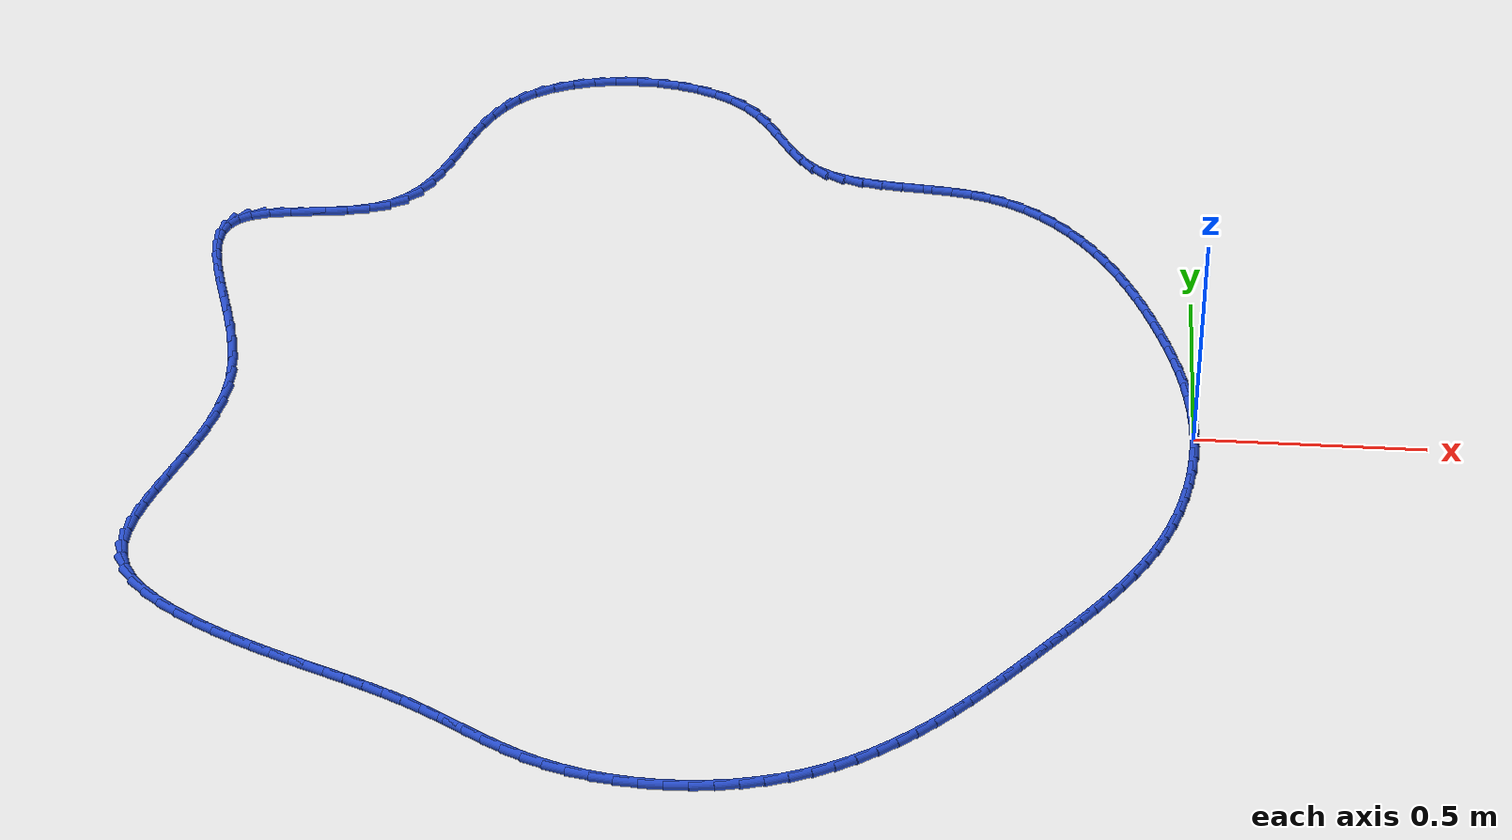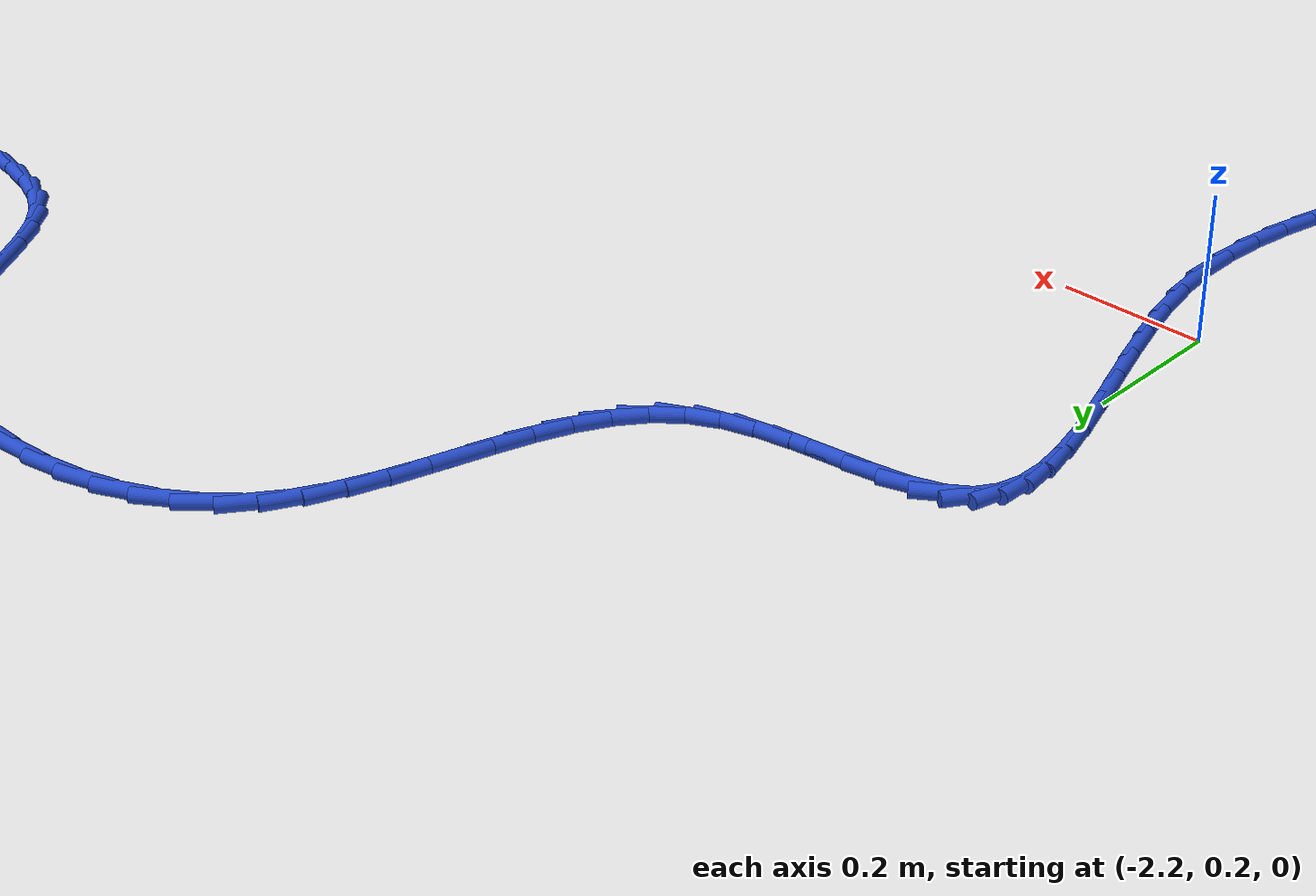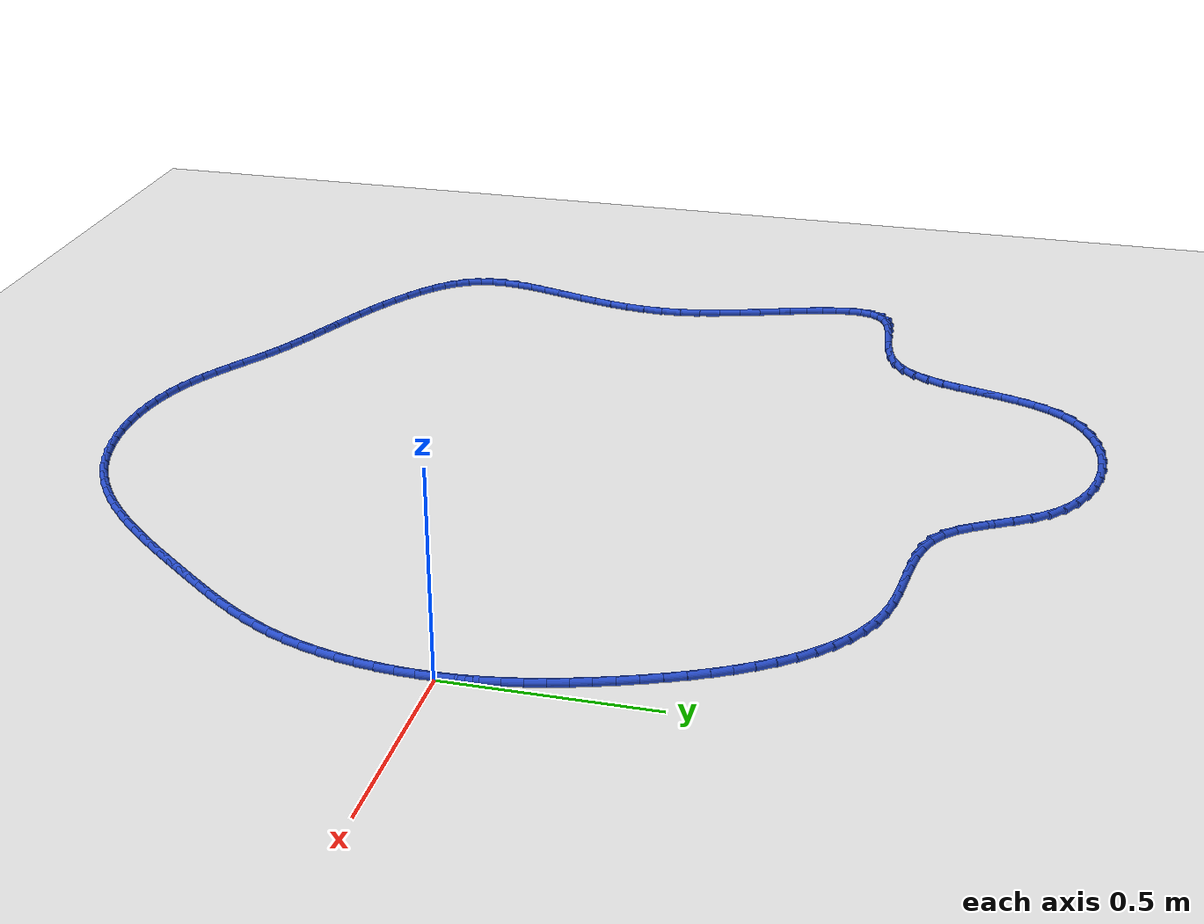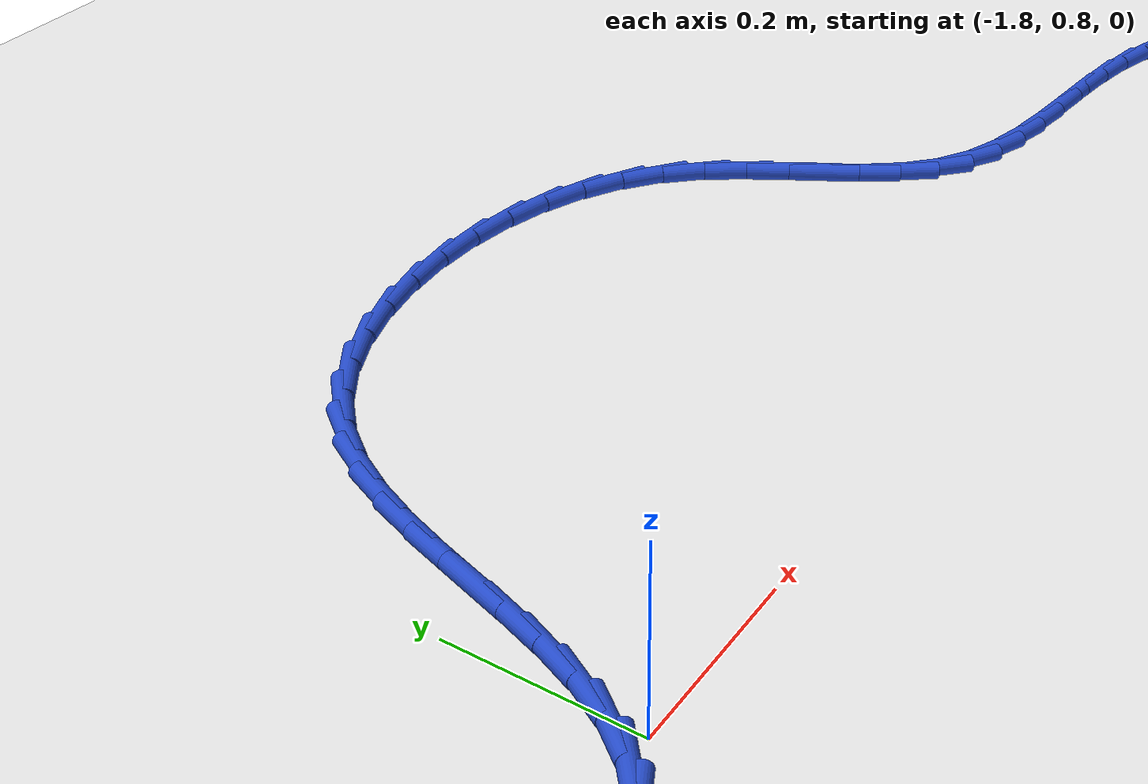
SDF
<sdf version="1.6">
 <world name="default">
  <light name="sun" type="directional">
   <pose>0 0 10 0 -0 0</pose>
   <diffuse>0.8 0.8 0.8 1</diffuse>
   <specular>0.2 0.2 0.2 1</specular>
   <attenuation>
    <range>1000</range>
    <constant>0.9</constant>
    <linear>0.01</linear>
    <quadratic>0.001</quadratic>
   </attenuation>
   <direction>-0.5 0.1 -0.9</direction>
  </light>
  <model name="ground_plane">
   <static>1</static>
   <link name="link">
    <collision name="collision">
     <geometry><plane><normal>0 0 1</normal><size>100 100</size></plane></geometry>
     <surface><friction><ode><mu>100</mu><mu2>50</mu2></ode></friction></surface>
    </collision>
    <visual name="visual">
     <cast_shadows>0</cast_shadows>
     <geometry><plane><normal>0 0 1</normal><size>100 100</size></plane></geometry>
     <material>
      <script><uri>file://media/materials/scripts/gazebo.material</uri><name>Gazebo/WhiteGlow</name></script>
     </material>
    </visual>
   </link>
  </model>
  <gravity>0 0 -9.8</gravity>
  <magnetic_field>6e-06 2.3e-05 -4.2e-05</magnetic_field>
  <atmosphere type="adiabatic"/>
  <physics name="default_physics" default="0" type="ode">
   <max_step_size>0.001</max_step_size>
   <real_time_factor>1</real_time_factor>
   <real_time_update_rate>1000</real_time_update_rate>
  </physics>
  <scene><ambient>0.4 0.4 0.4 1</ambient><background>0.7 0.7 0.7 1</background><shadows>1</shadows></scene>
  <spherical_coordinates>
   <surface_model>EARTH_WGS84</surface_model>
   <latitude_deg>0</latitude_deg>
   <longitude_deg>0</longitude_deg>
   <elevation>0</elevation>
   <heading_deg>0</heading_deg>
  </spherical_coordinates>
  <model name="line">
   <link name="link_0">
    <pose>1.0408340855860843e-17 1.6653345369377348e-16 0.01 0 1.57 -1.5307785798557336</pose>
    <collision name="collision">
     <geometry><cylinder><radius>0.01</radius><length>0.08</length></cylinder></geometry>
    </collision>
    <visual name="visual">
     <material>
      <script><name>Gazebo/Blue</name><uri>file://media/materials/scripts/gazebo.material</uri></script>
     </material>
     <geometry><cylinder><radius>0.01</radius><length>0.08</length></cylinder></geometry>
    </visual>
   </link>
   <link name="link_1">
    <pose>-0.001858721512014307 0.04642263371088782 0.01 0 1.57 -1.4824107533614235</pose>
    <collision name="collision">
     <geometry><cylinder><radius>0.01</radius><length>0.08</length></cylinder></geometry>
    </collision>
    <visual name="visual">
     <material>
      <script><name>Gazebo/Blue</name><uri>file://media/materials/scripts/gazebo.material</uri></script>
     </material>
     <geometry><cylinder><radius>0.01</radius><length>0.08</length></cylinder></geometry>
    </visual>
   </link>
   <link name="link_2">
    <pose>-0.005940966023274526 0.0924890745904151 0.01 0 1.57 -1.436435670266301</pose>
    <collision name="collision">
     <geometry><cylinder><radius>0.01</radius><length>0.08</length></cylinder></geometry>
    </collision>
    <visual name="visual">
     <material>
      <script><name>Gazebo/Blue</name><uri>file://media/materials/scripts/gazebo.material</uri></script>
     </material>
     <geometry><cylinder><radius>0.01</radius><length>0.08</length></cylinder></geometry>
    </visual>
   </link>
   <link name="link_3">
    <pose>-0.012134233433535868 0.13830571512713555 0.01 0 1.57 -1.3933267834648728</pose>
    <collision name="collision">
     <geometry><cylinder><radius>0.01</radius><length>0.08</length></cylinder></geometry>
    </collision>
    <visual name="visual">
     <material>
      <script><name>Gazebo/Blue</name><uri>file://media/materials/scripts/gazebo.material</uri></script>
     </material>
     <geometry><cylinder><radius>0.01</radius><length>0.08</length></cylinder></geometry>
    </visual>
   </link>
   <link name="link_4">
    <pose>-0.020326023642553544 0.18397894780960256 0.01 0 1.57 -1.3534551659874263</pose>
    <collision name="collision">
     <geometry><cylinder><radius>0.01</radius><length>0.08</length></cylinder></geometry>
    </collision>
    <visual name="visual">
     <material>
      <script><name>Gazebo/Blue</name><uri>file://media/materials/scripts/gazebo.material</uri></script>
     </material>
     <geometry><cylinder><radius>0.01</radius><length>0.08</length></cylinder></geometry>
    </visual>
   </link>
   <link name="link_5">
    <pose>-0.030403836550082778 0.22961516512636976 0.01 0 1.57 -1.3170866215379182</pose>
    <collision name="collision">
     <geometry><cylinder><radius>0.01</radius><length>0.08</length></cylinder></geometry>
    </collision>
    <visual name="visual">
     <material>
      <script><name>Gazebo/Blue</name><uri>file://media/materials/scripts/gazebo.material</uri></script>
     </material>
     <geometry><cylinder><radius>0.01</radius><length>0.08</length></cylinder></geometry>
    </visual>
   </link>
   <link name="link_6">
    <pose>-0.042255172055878795 0.27532075956599067 0.01 0 1.57 -1.2843870683193195</pose>
    <collision name="collision">
     <geometry><cylinder><radius>0.01</radius><length>0.08</length></cylinder></geometry>
    </collision>
    <visual name="visual">
     <material>
      <script><name>Gazebo/Blue</name><uri>file://media/materials/scripts/gazebo.material</uri></script>
     </material>
     <geometry><cylinder><radius>0.01</radius><length>0.08</length></cylinder></geometry>
    </visual>
   </link>
   <link name="link_7">
    <pose>-0.055767530059696785 0.32120212361701855 0.01 0 1.57 -1.255433673963761</pose>
    <collision name="collision">
     <geometry><cylinder><radius>0.01</radius><length>0.08</length></cylinder></geometry>
    </collision>
    <visual name="visual">
     <material>
      <script><name>Gazebo/Blue</name><uri>file://media/materials/scripts/gazebo.material</uri></script>
     </material>
     <geometry><cylinder><radius>0.01</radius><length>0.08</length></cylinder></geometry>
    </visual>
   </link>
   <link name="link_8">
    <pose>-0.07082841046129197 0.367365649768007 0.01 0 1.57 -1.2298542153299223</pose>
    <collision name="collision">
     <geometry><cylinder><radius>0.01</radius><length>0.08</length></cylinder></geometry>
    </collision>
    <visual name="visual">
     <material>
      <script><name>Gazebo/Blue</name><uri>file://media/materials/scripts/gazebo.material</uri></script>
     </material>
     <geometry><cylinder><radius>0.01</radius><length>0.08</length></cylinder></geometry>
    </visual>
   </link>
   <link name="link_9">
    <pose>-0.08733602795371681 0.41389255619519905 0.01 0 1.57 -1.2032316690330587</pose>
    <collision name="collision">
     <geometry><cylinder><radius>0.01</radius><length>0.08</length></cylinder></geometry>
    </collision>
    <visual name="visual">
     <material>
      <script><name>Gazebo/Blue</name><uri>file://media/materials/scripts/gazebo.material</uri></script>
     </material>
     <geometry><cylinder><radius>0.01</radius><length>0.08</length></cylinder></geometry>
    </visual>
   </link>
   <link name="link_10">
    <pose>-0.1053116979493797 0.4605748370208803 0.01 0 1.57 -1.1724911542365255</pose>
    <collision name="collision">
     <geometry><cylinder><radius>0.01</radius><length>0.08</length></cylinder></geometry>
    </collision>
    <visual name="visual">
     <material>
      <script><name>Gazebo/Blue</name><uri>file://media/materials/scripts/gazebo.material</uri></script>
     </material>
     <geometry><cylinder><radius>0.01</radius><length>0.08</length></cylinder></geometry>
    </visual>
   </link>
   <link name="link_11">
    <pose>-0.12485546845025954 0.5070195048428323 0.01 0 1.57 -1.137136139844849</pose>
    <collision name="collision">
     <geometry><cylinder><radius>0.01</radius><length>0.08</length></cylinder></geometry>
    </collision>
    <visual name="visual">
     <material>
      <script><name>Gazebo/Blue</name><uri>file://media/materials/scripts/gazebo.material</uri></script>
     </material>
     <geometry><cylinder><radius>0.01</radius><length>0.08</length></cylinder></geometry>
    </visual>
   </link>
   <link name="link_12">
    <pose>-0.14606866913526717 0.5528305609701929 0.01 0 1.57 -1.0966070510772625</pose>
    <collision name="collision">
     <geometry><cylinder><radius>0.01</radius><length>0.08</length></cylinder></geometry>
    </collision>
    <visual name="visual">
     <material>
      <script><name>Gazebo/Blue</name><uri>file://media/materials/scripts/gazebo.material</uri></script>
     </material>
     <geometry><cylinder><radius>0.01</radius><length>0.08</length></cylinder></geometry>
    </visual>
   </link>
   <link name="link_13">
    <pose>-0.16905262968331358 0.5976120067121005 0.01 0 1.57 -1.0502379953094667</pose>
    <collision name="collision">
     <geometry><cylinder><radius>0.01</radius><length>0.08</length></cylinder></geometry>
    </collision>
    <visual name="visual">
     <material>
      <script><name>Gazebo/Blue</name><uri>file://media/materials/scripts/gazebo.material</uri></script>
     </material>
     <geometry><cylinder><radius>0.01</radius><length>0.08</length></cylinder></geometry>
    </visual>
   </link>
   <link name="link_14">
    <pose>-0.19390867977330972 0.6409678433776929 0.01 0 1.57 -0.9972661018475963</pose>
    <collision name="collision">
     <geometry><cylinder><radius>0.01</radius><length>0.08</length></cylinder></geometry>
    </collision>
    <visual name="visual">
     <material>
      <script><name>Gazebo/Blue</name><uri>file://media/materials/scripts/gazebo.material</uri></script>
     </material>
     <geometry><cylinder><radius>0.01</radius><length>0.08</length></cylinder></geometry>
    </visual>
   </link>
   <link name="link_15">
    <pose>-0.22073814908416645 0.6825020722761085 0.01 0 1.57 -0.9368571966738959</pose>
    <collision name="collision">
     <geometry><cylinder><radius>0.01</radius><length>0.08</length></cylinder></geometry>
    </collision>
    <visual name="visual">
     <material>
      <script><name>Gazebo/Blue</name><uri>file://media/materials/scripts/gazebo.material</uri></script>
     </material>
     <geometry><cylinder><radius>0.01</radius><length>0.08</length></cylinder></geometry>
    </visual>
   </link>
   <link name="link_16">
    <pose>-0.24964236729479475 0.7218186947164852 0.01 0 1.57 -0.8681600796457231</pose>
    <collision name="collision">
     <geometry><cylinder><radius>0.01</radius><length>0.08</length></cylinder></geometry>
    </collision>
    <visual name="visual">
     <material>
      <script><name>Gazebo/Blue</name><uri>file://media/materials/scripts/gazebo.material</uri></script>
     </material>
     <geometry><cylinder><radius>0.01</radius><length>0.08</length></cylinder></geometry>
    </visual>
   </link>
   <link name="link_17">
    <pose>-0.2807226640841055 0.7585217120079611 0.01 0 1.57 -0.7904048748026672</pose>
    <collision name="collision">
     <geometry><cylinder><radius>0.01</radius><length>0.08</length></cylinder></geometry>
    </collision>
    <visual name="visual">
     <material>
      <script><name>Gazebo/Blue</name><uri>file://media/materials/scripts/gazebo.material</uri></script>
     </material>
     <geometry><cylinder><radius>0.01</radius><length>0.08</length></cylinder></geometry>
    </visual>
   </link>
   <link name="link_18">
    <pose>-0.3140803691310096 0.792215125459675 0.01 0 1.57 -0.7030600368776598</pose>
    <collision name="collision">
     <geometry><cylinder><radius>0.01</radius><length>0.08</length></cylinder></geometry>
    </collision>
    <visual name="visual">
     <material>
      <script><name>Gazebo/Blue</name><uri>file://media/materials/scripts/gazebo.material</uri></script>
     </material>
     <geometry><cylinder><radius>0.01</radius><length>0.08</length></cylinder></geometry>
    </visual>
   </link>
   <link name="link_19">
    <pose>-0.34981681211441806 0.822502936380764 0.01 0 1.57 -0.6060508326332041</pose>
    <collision name="collision">
     <geometry><cylinder><radius>0.01</radius><length>0.08</length></cylinder></geometry>
    </collision>
    <visual name="visual">
     <material>
      <script><name>Gazebo/Blue</name><uri>file://media/materials/scripts/gazebo.material</uri></script>
     </material>
     <geometry><cylinder><radius>0.01</radius><length>0.08</length></cylinder></geometry>
    </visual>
   </link>
   <link name="link_20">
    <pose>-0.3880333227132417 0.8489891460803671 0.01 0 1.57 -0.5000115362658203</pose>
    <collision name="collision">
     <geometry><cylinder><radius>0.01</radius><length>0.08</length></cylinder></geometry>
    </collision>
    <visual name="visual">
     <material>
      <script><name>Gazebo/Blue</name><uri>file://media/materials/scripts/gazebo.material</uri></script>
     </material>
     <geometry><cylinder><radius>0.01</radius><length>0.08</length></cylinder></geometry>
    </visual>
   </link>
   <link name="link_21">
    <pose>-0.42883123060639156 0.871277755867622 0.01 0 1.57 -0.3864945449638289</pose>
    <collision name="collision">
     <geometry><cylinder><radius>0.01</radius><length>0.08</length></cylinder></geometry>
    </collision>
    <visual name="visual">
     <material>
      <script><name>Gazebo/Blue</name><uri>file://media/materials/scripts/gazebo.material</uri></script>
     </material>
     <geometry><cylinder><radius>0.01</radius><length>0.08</length></cylinder></geometry>
    </visual>
   </link>
   <link name="link_22">
    <pose>-0.47231186547277854 0.888972767051667 0.01 0 1.57 -0.2700500714416034</pose>
    <collision name="collision">
     <geometry><cylinder><radius>0.01</radius><length>0.08</length></cylinder></geometry>
    </collision>
    <visual name="visual">
     <material>
      <script><name>Gazebo/Blue</name><uri>file://media/materials/scripts/gazebo.material</uri></script>
     </material>
     <geometry><cylinder><radius>0.01</radius><length>0.08</length></cylinder></geometry>
    </visual>
   </link>
   <link name="link_23">
    <pose>-0.5185269437244302 0.9017656572932711 0.01 0 1.57 -0.17718210906850276</pose>
    <collision name="collision">
     <geometry><cylinder><radius>0.01</radius><length>0.08</length></cylinder></geometry>
    </collision>
    <visual name="visual">
     <material>
      <script><name>Gazebo/Blue</name><uri>file://media/materials/scripts/gazebo.material</uri></script>
     </material>
     <geometry><cylinder><radius>0.01</radius><length>0.08</length></cylinder></geometry>
    </visual>
   </link>
   <link name="link_24">
    <pose>-0.5669145010639884 0.9104299243034026 0.01 0 1.57 -0.12120529322183834</pose>
    <collision name="collision">
     <geometry><cylinder><radius>0.01</radius><length>0.08</length></cylinder></geometry>
    </collision>
    <visual name="visual">
     <material>
      <script><name>Gazebo/Blue</name><uri>file://media/materials/scripts/gazebo.material</uri></script>
     </material>
     <geometry><cylinder><radius>0.01</radius><length>0.08</length></cylinder></geometry>
    </visual>
   </link>
   <link name="link_25">
    <pose>-0.6164983800525924 0.9164693564423926 0.01 0 1.57 -0.09872338030837678</pose>
    <collision name="collision">
     <geometry><cylinder><radius>0.01</radius><length>0.08</length></cylinder></geometry>
    </collision>
    <visual name="visual">
     <material>
      <script><name>Gazebo/Blue</name><uri>file://media/materials/scripts/gazebo.material</uri></script>
     </material>
     <geometry><cylinder><radius>0.01</radius><length>0.08</length></cylinder></geometry>
    </visual>
   </link>
   <link name="link_26">
    <pose>-0.6662946507593727 0.9214014462526762 0.01 0 1.57 -0.10854202803596015</pose>
    <collision name="collision">
     <geometry><cylinder><radius>0.01</radius><length>0.08</length></cylinder></geometry>
    </collision>
    <visual name="visual">
     <material>
      <script><name>Gazebo/Blue</name><uri>file://media/materials/scripts/gazebo.material</uri></script>
     </material>
     <geometry><cylinder><radius>0.01</radius><length>0.08</length></cylinder></geometry>
    </visual>
   </link>
   <link name="link_27">
    <pose>-0.7153193832534586 0.9267436862766889 0.01 0 1.57 -0.15260155313605617</pose>
    <collision name="collision">
     <geometry><cylinder><radius>0.01</radius><length>0.08</length></cylinder></geometry>
    </collision>
    <visual name="visual">
     <material>
      <script><name>Gazebo/Blue</name><uri>file://media/materials/scripts/gazebo.material</uri></script>
     </material>
     <geometry><cylinder><radius>0.01</radius><length>0.08</length></cylinder></geometry>
    </visual>
   </link>
   <link name="link_28">
    <pose>-0.7625886476039796 0.9340135690568666 0.01 0 1.57 -0.2361362609698178</pose>
    <collision name="collision">
     <geometry><cylinder><radius>0.01</radius><length>0.08</length></cylinder></geometry>
    </collision>
    <visual name="visual">
     <material>
      <script><name>Gazebo/Blue</name><uri>file://media/materials/scripts/gazebo.material</uri></script>
     </material>
     <geometry><cylinder><radius>0.01</radius><length>0.08</length></cylinder></geometry>
    </visual>
   </link>
   <link name="link_29">
    <pose>-0.8071185138800653 0.9447285871356441 0.01 0 1.57 -0.3668071000280431</pose>
    <collision name="collision">
     <geometry><cylinder><radius>0.01</radius><length>0.08</length></cylinder></geometry>
    </collision>
    <visual name="visual">
     <material>
      <script><name>Gazebo/Blue</name><uri>file://media/materials/scripts/gazebo.material</uri></script>
     </material>
     <geometry><cylinder><radius>0.01</radius><length>0.08</length></cylinder></geometry>
    </visual>
   </link>
   <link name="link_30">
    <pose>-0.8479250521508455 0.9604062330554574 0.01 0 1.57 -0.5505053773676107</pose>
    <collision name="collision">
     <geometry><cylinder><radius>0.01</radius><length>0.08</length></cylinder></geometry>
    </collision>
    <visual name="visual">
     <material>
      <script><name>Gazebo/Blue</name><uri>file://media/materials/scripts/gazebo.material</uri></script>
     </material>
     <geometry><cylinder><radius>0.01</radius><length>0.08</length></cylinder></geometry>
    </visual>
   </link>
   <link name="link_31">
    <pose>-0.8840243324854496 0.9825639993587416 0.01 0 1.57 -0.7664154667194171</pose>
    <collision name="collision">
     <geometry><cylinder><radius>0.01</radius><length>0.08</length></cylinder></geometry>
    </collision>
    <visual name="visual">
     <material>
      <script><name>Gazebo/Blue</name><uri>file://media/materials/scripts/gazebo.material</uri></script>
     </material>
     <geometry><cylinder><radius>0.01</radius><length>0.08</length></cylinder></geometry>
    </visual>
   </link>
   <link name="link_32">
    <pose>-0.9148237621297316 1.0122157644552476 0.01 0 1.57 -0.9291367369747572</pose>
    <collision name="collision">
     <geometry><cylinder><radius>0.01</radius><length>0.08</length></cylinder></geometry>
    </collision>
    <visual name="visual">
     <material>
      <script><name>Gazebo/Blue</name><uri>file://media/materials/scripts/gazebo.material</uri></script>
     </material>
     <geometry><cylinder><radius>0.01</radius><length>0.08</length></cylinder></geometry>
    </visual>
   </link>
   <link name="link_33">
    <pose>-0.9415676746747503 1.0480114553512532 0.01 0 1.57 -1.0206057435527836</pose>
    <collision name="collision">
     <geometry><cylinder><radius>0.01</radius><length>0.08</length></cylinder></geometry>
    </collision>
    <visual name="visual">
     <material>
      <script><name>Gazebo/Blue</name><uri>file://media/materials/scripts/gazebo.material</uri></script>
     </material>
     <geometry><cylinder><radius>0.01</radius><length>0.08</length></cylinder></geometry>
    </visual>
   </link>
   <link name="link_34">
    <pose>-0.9660389113272696 1.087907990409961 0.01 0 1.57 -1.0515129740956561</pose>
    <collision name="collision">
     <geometry><cylinder><radius>0.01</radius><length>0.08</length></cylinder></geometry>
    </collision>
    <visual name="visual">
     <material>
      <script><name>Gazebo/Blue</name><uri>file://media/materials/scripts/gazebo.material</uri></script>
     </material>
     <geometry><cylinder><radius>0.01</radius><length>0.08</length></cylinder></geometry>
    </visual>
   </link>
   <link name="link_35">
    <pose>-0.9900203828883766 1.1298621984332236 0.01 0 1.57 -1.028742210296648</pose>
    <collision name="collision">
     <geometry><cylinder><radius>0.01</radius><length>0.08</length></cylinder></geometry>
    </collision>
    <visual name="visual">
     <material>
      <script><name>Gazebo/Blue</name><uri>file://media/materials/scripts/gazebo.material</uri></script>
     </material>
     <geometry><cylinder><radius>0.01</radius><length>0.08</length></cylinder></geometry>
    </visual>
   </link>
   <link name="link_36">
    <pose>-1.0152950001591592 1.1718309082228957 0.01 0 1.57 -0.9535028868978923</pose>
    <collision name="collision">
     <geometry><cylinder><radius>0.01</radius><length>0.08</length></cylinder></geometry>
    </collision>
    <visual name="visual">
     <material>
      <script><name>Gazebo/Blue</name><uri>file://media/materials/scripts/gazebo.material</uri></script>
     </material>
     <geometry><cylinder><radius>0.01</radius><length>0.08</length></cylinder></geometry>
    </visual>
   </link>
   <link name="link_37">
    <pose>-1.0436456739407047 1.2117709485808306 0.01 0 1.57 -0.8239366933005705</pose>
    <collision name="collision">
     <geometry><cylinder><radius>0.01</radius><length>0.08</length></cylinder></geometry>
    </collision>
    <visual name="visual">
     <material>
      <script><name>Gazebo/Blue</name><uri>file://media/materials/scripts/gazebo.material</uri></script>
     </material>
     <geometry><cylinder><radius>0.01</radius><length>0.08</length></cylinder></geometry>
    </visual>
   </link>
   <link name="link_38">
    <pose>-1.0768524610542503 1.2476411812154706 0.01 0 1.57 -0.6598890937508796</pose>
    <collision name="collision">
     <geometry><cylinder><radius>0.01</radius><length>0.08</length></cylinder></geometry>
    </collision>
    <visual name="visual">
     <material>
      <script><name>Gazebo/Blue</name><uri>file://media/materials/scripts/gazebo.material</uri></script>
     </material>
     <geometry><cylinder><radius>0.01</radius><length>0.08</length></cylinder></geometry>
    </visual>
   </link>
   <link name="link_39">
    <pose>-1.1159186929473652 1.2779537338752536 0.01 0 1.57 -0.5082415198840071</pose>
    <collision name="collision">
     <geometry><cylinder><radius>0.01</radius><length>0.08</length></cylinder></geometry>
    </collision>
    <visual name="visual">
     <material>
      <script><name>Gazebo/Blue</name><uri>file://media/materials/scripts/gazebo.material</uri></script>
     </material>
     <geometry><cylinder><radius>0.01</radius><length>0.08</length></cylinder></geometry>
    </visual>
   </link>
   <link name="link_40">
    <pose>-1.1600216921079205 1.302521411202123 0.01 0 1.57 -0.37331695636103357</pose>
    <collision name="collision">
     <geometry><cylinder><radius>0.01</radius><length>0.08</length></cylinder></geometry>
    </collision>
    <visual name="visual">
     <material>
      <script><name>Gazebo/Blue</name><uri>file://media/materials/scripts/gazebo.material</uri></script>
     </material>
     <geometry><cylinder><radius>0.01</radius><length>0.08</length></cylinder></geometry>
    </visual>
   </link>
   <link name="link_41">
    <pose>-1.208076617290044 1.3213437586034407 0.01 0 1.57 -0.2513644970746795</pose>
    <collision name="collision">
     <geometry><cylinder><radius>0.01</radius><length>0.08</length></cylinder></geometry>
    </collision>
    <visual name="visual">
     <material>
      <script><name>Gazebo/Blue</name><uri>file://media/materials/scripts/gazebo.material</uri></script>
     </material>
     <geometry><cylinder><radius>0.01</radius><length>0.08</length></cylinder></geometry>
    </visual>
   </link>
   <link name="link_42">
    <pose>-1.2589986272478628 1.3344203214865673 0.01 0 1.57 -0.13819753733453533</pose>
    <collision name="collision">
     <geometry><cylinder><radius>0.01</radius><length>0.08</length></cylinder></geometry>
    </collision>
    <visual name="visual">
     <material>
      <script><name>Gazebo/Blue</name><uri>file://media/materials/scripts/gazebo.material</uri></script>
     </material>
     <geometry><cylinder><radius>0.01</radius><length>0.08</length></cylinder></geometry>
    </visual>
   </link>
   <link name="link_43">
    <pose>-1.3117028807355051 1.3417506452588648 0.01 0 1.57 -0.02964638574633757</pose>
    <collision name="collision">
     <geometry><cylinder><radius>0.01</radius><length>0.08</length></cylinder></geometry>
    </collision>
    <visual name="visual">
     <material>
      <script><name>Gazebo/Blue</name><uri>file://media/materials/scripts/gazebo.material</uri></script>
     </material>
     <geometry><cylinder><radius>0.01</radius><length>0.08</length></cylinder></geometry>
    </visual>
   </link>
   <link name="link_44">
    <pose>-1.3651045365070988 1.3433342753276944 0.01 0 1.57 0.07837500926084524</pose>
    <collision name="collision">
     <geometry><cylinder><radius>0.01</radius><length>0.08</length></cylinder></geometry>
    </collision>
    <visual name="visual">
     <material>
      <script><name>Gazebo/Blue</name><uri>file://media/materials/scripts/gazebo.material</uri></script>
     </material>
     <geometry><cylinder><radius>0.01</radius><length>0.08</length></cylinder></geometry>
    </visual>
   </link>
   <link name="link_45">
    <pose>-1.4181187533167712 1.3391707571004179 0.01 0 1.57 0.1899735114983352</pose>
    <collision name="collision">
     <geometry><cylinder><radius>0.01</radius><length>0.08</length></cylinder></geometry>
    </collision>
    <visual name="visual">
     <material>
      <script><name>Gazebo/Blue</name><uri>file://media/materials/scripts/gazebo.material</uri></script>
     </material>
     <geometry><cylinder><radius>0.01</radius><length>0.08</length></cylinder></geometry>
    </visual>
   </link>
   <link name="link_46">
    <pose>-1.4696606899186506 1.3292596359843967 0.01 0 1.57 0.30940732407456734</pose>
    <collision name="collision">
     <geometry><cylinder><radius>0.01</radius><length>0.08</length></cylinder></geometry>
    </collision>
    <visual name="visual">
     <material>
      <script><name>Gazebo/Blue</name><uri>file://media/materials/scripts/gazebo.material</uri></script>
     </material>
     <geometry><cylinder><radius>0.01</radius><length>0.08</length></cylinder></geometry>
    </visual>
   </link>
   <link name="link_47">
    <pose>-1.518645505066864 1.3136004573869922 0.01 0 1.57 0.4411035251607573</pose>
    <collision name="collision">
     <geometry><cylinder><radius>0.01</radius><length>0.08</length></cylinder></geometry>
    </collision>
    <visual name="visual">
     <material>
      <script><name>Gazebo/Blue</name><uri>file://media/materials/scripts/gazebo.material</uri></script>
     </material>
     <geometry><cylinder><radius>0.01</radius><length>0.08</length></cylinder></geometry>
    </visual>
   </link>
   <link name="link_48">
    <pose>-1.5639883575155396 1.2921927667155657 0.01 0 1.57 0.5893529265007421</pose>
    <collision name="collision">
     <geometry><cylinder><radius>0.01</radius><length>0.08</length></cylinder></geometry>
    </collision>
    <visual name="visual">
     <material>
      <script><name>Gazebo/Blue</name><uri>file://media/materials/scripts/gazebo.material</uri></script>
     </material>
     <geometry><cylinder><radius>0.01</radius><length>0.08</length></cylinder></geometry>
    </visual>
   </link>
   <link name="link_49">
    <pose>-1.604604406018804 1.2650361093774787 0.01 0 1.57 0.7573602692474132</pose>
    <collision name="collision">
     <geometry><cylinder><radius>0.01</radius><length>0.08</length></cylinder></geometry>
    </collision>
    <visual name="visual">
     <material>
      <script><name>Gazebo/Blue</name><uri>file://media/materials/scripts/gazebo.material</uri></script>
     </material>
     <geometry><cylinder><radius>0.01</radius><length>0.08</length></cylinder></geometry>
    </visual>
   </link>
   <link name="link_50">
    <pose>-1.6394092319172884 1.232130246243419 0.01 0 1.57 0.933192259167531</pose>
    <collision name="collision">
     <geometry><cylinder><radius>0.01</radius><length>0.08</length></cylinder></geometry>
    </collision>
    <visual name="visual">
     <material>
      <script><name>Gazebo/Blue</name><uri>file://media/materials/scripts/gazebo.material</uri></script>
     </material>
     <geometry><cylinder><radius>0.01</radius><length>0.08</length></cylinder></geometry>
    </visual>
   </link>
   <link name="link_51">
    <pose>-1.66784659632492 1.1937442401378657 0.01 0 1.57 1.0763899878214525</pose>
    <collision name="collision">
     <geometry><cylinder><radius>0.01</radius><length>0.08</length></cylinder></geometry>
    </collision>
    <visual name="visual">
     <material>
      <script><name>Gazebo/Blue</name><uri>file://media/materials/scripts/gazebo.material</uri></script>
     </material>
     <geometry><cylinder><radius>0.01</radius><length>0.08</length></cylinder></geometry>
    </visual>
   </link>
   <link name="link_52">
    <pose>-1.6909195380726676 1.1509421796642714 0.01 0 1.57 1.1791969337913202</pose>
    <collision name="collision">
     <geometry><cylinder><radius>0.01</radius><length>0.08</length></cylinder></geometry>
    </collision>
    <visual name="visual">
     <material>
      <script><name>Gazebo/Blue</name><uri>file://media/materials/scripts/gazebo.material</uri></script>
     </material>
     <geometry><cylinder><radius>0.01</radius><length>0.08</length></cylinder></geometry>
    </visual>
   </link>
   <link name="link_53">
    <pose>-1.7099174394261816 1.104934150774555 0.01 0 1.57 1.2450962072886174</pose>
    <collision name="collision">
     <geometry><cylinder><radius>0.01</radius><length>0.08</length></cylinder></geometry>
    </collision>
    <visual name="visual">
     <material>
      <script><name>Gazebo/Blue</name><uri>file://media/materials/scripts/gazebo.material</uri></script>
     </material>
     <geometry><cylinder><radius>0.01</radius><length>0.08</length></cylinder></geometry>
    </visual>
   </link>
   <link name="link_54">
    <pose>-1.7261296826511143 1.0569302394206368 0.01 0 1.57 1.2778536627604544</pose>
    <collision name="collision">
     <geometry><cylinder><radius>0.01</radius><length>0.08</length></cylinder></geometry>
    </collision>
    <visual name="visual">
     <material>
      <script><name>Gazebo/Blue</name><uri>file://media/materials/scripts/gazebo.material</uri></script>
     </material>
     <geometry><cylinder><radius>0.01</radius><length>0.08</length></cylinder></geometry>
    </visual>
   </link>
   <link name="link_55">
    <pose>-1.7408456500131162 1.008140531554436 0.01 0 1.57 1.279349998605101</pose>
    <collision name="collision">
     <geometry><cylinder><radius>0.01</radius><length>0.08</length></cylinder></geometry>
    </collision>
    <visual name="visual">
     <material>
      <script><name>Gazebo/Blue</name><uri>file://media/materials/scripts/gazebo.material</uri></script>
     </material>
     <geometry><cylinder><radius>0.01</radius><length>0.08</length></cylinder></geometry>
    </visual>
   </link>
   <link name="link_56">
    <pose>-1.7553547237778397 0.959775113127872 0.01 0 1.57 1.2487656148121244</pose>
    <collision name="collision">
     <geometry><cylinder><radius>0.01</radius><length>0.08</length></cylinder></geometry>
    </collision>
    <visual name="visual">
     <material>
      <script><name>Gazebo/Blue</name><uri>file://media/materials/scripts/gazebo.material</uri></script>
     </material>
     <geometry><cylinder><radius>0.01</radius><length>0.08</length></cylinder></geometry>
    </visual>
   </link>
   <link name="link_57">
    <pose>-1.770946286210935 0.9130440700928651 0.01 0 1.57 1.1822857140928773</pose>
    <collision name="collision">
     <geometry><cylinder><radius>0.01</radius><length>0.08</length></cylinder></geometry>
    </collision>
    <visual name="visual">
     <material>
      <script><name>Gazebo/Blue</name><uri>file://media/materials/scripts/gazebo.material</uri></script>
     </material>
     <geometry><cylinder><radius>0.01</radius><length>0.08</length></cylinder></geometry>
    </visual>
   </link>
   <link name="link_58">
    <pose>-1.7889097195780548 0.8691574884013341 0.01 0 1.57 1.0734229308855177</pose>
    <collision name="collision">
     <geometry><cylinder><radius>0.01</radius><length>0.08</length></cylinder></geometry>
    </collision>
    <visual name="visual">
     <material>
      <script><name>Gazebo/Blue</name><uri>file://media/materials/scripts/gazebo.material</uri></script>
     </material>
     <geometry><cylinder><radius>0.01</radius><length>0.08</length></cylinder></geometry>
    </visual>
   </link>
   <link name="link_59">
    <pose>-1.8105344061448496 0.8293254540051996 0.01 0 1.57 0.9153731338447192</pose>
    <collision name="collision">
     <geometry><cylinder><radius>0.01</radius><length>0.08</length></cylinder></geometry>
    </collision>
    <visual name="visual">
     <material>
      <script><name>Gazebo/Blue</name><uri>file://media/materials/scripts/gazebo.material</uri></script>
     </material>
     <geometry><cylinder><radius>0.01</radius><length>0.08</length></cylinder></geometry>
    </visual>
   </link>
   <link name="link_60">
    <pose>-1.837109728176971 0.7947580528563803 0.01 0 1.57 0.7080154581325362</pose>
    <collision name="collision">
     <geometry><cylinder><radius>0.01</radius><length>0.08</length></cylinder></geometry>
    </collision>
    <visual name="visual">
     <material>
      <script><name>Gazebo/Blue</name><uri>file://media/materials/scripts/gazebo.material</uri></script>
     </material>
     <geometry><cylinder><radius>0.01</radius><length>0.08</length></cylinder></geometry>
    </visual>
   </link>
   <link name="link_61">
    <pose>-1.8699250679400703 0.7666653709067959 0.01 0 1.57 0.47150130983645266</pose>
    <collision name="collision">
     <geometry><cylinder><radius>0.01</radius><length>0.08</length></cylinder></geometry>
    </collision>
    <visual name="visual">
     <material>
      <script><name>Gazebo/Blue</name><uri>file://media/materials/scripts/gazebo.material</uri></script>
     </material>
     <geometry><cylinder><radius>0.01</radius><length>0.08</length></cylinder></geometry>
    </visual>
   </link>
   <link name="link_62">
    <pose>-1.9101500622862586 0.7461564149082507 0.01 0 1.57 0.28336937954209</pose>
    <collision name="collision">
     <geometry><cylinder><radius>0.01</radius><length>0.08</length></cylinder></geometry>
    </collision>
    <visual name="visual">
     <material>
      <script><name>Gazebo/Blue</name><uri>file://media/materials/scripts/gazebo.material</uri></script>
     </material>
     <geometry><cylinder><radius>0.01</radius><length>0.08</length></cylinder></geometry>
    </visual>
   </link>
   <link name="link_63">
    <pose>-1.9568440498897803 0.732558851972728 0.01 0 1.57 0.1743750322196133</pose>
    <collision name="collision">
     <geometry><cylinder><radius>0.01</radius><length>0.08</length></cylinder></geometry>
    </collision>
    <visual name="visual">
     <material>
      <script><name>Gazebo/Blue</name><uri>file://media/materials/scripts/gazebo.material</uri></script>
     </material>
     <geometry><cylinder><radius>0.01</radius><length>0.08</length></cylinder></geometry>
    </visual>
   </link>
   <link name="link_64">
    <pose>-2.007261770244827 0.7236770554487428 0.01 0 1.57 0.12422981429136444</pose>
    <collision name="collision">
     <geometry><cylinder><radius>0.01</radius><length>0.08</length></cylinder></geometry>
    </collision>
    <visual name="visual">
     <material>
      <script><name>Gazebo/Blue</name><uri>file://media/materials/scripts/gazebo.material</uri></script>
     </material>
     <geometry><cylinder><radius>0.01</radius><length>0.08</length></cylinder></geometry>
    </visual>
   </link>
   <link name="link_65">
    <pose>-2.0585998269771535 0.717266325180396 0.01 0 1.57 0.12440456002004267</pose>
    <collision name="collision">
     <geometry><cylinder><radius>0.01</radius><length>0.08</length></cylinder></geometry>
    </collision>
    <visual name="visual">
     <material>
      <script><name>Gazebo/Blue</name><uri>file://media/materials/scripts/gazebo.material</uri></script>
     </material>
     <geometry><cylinder><radius>0.01</radius><length>0.08</length></cylinder></geometry>
    </visual>
   </link>
   <link name="link_66">
    <pose>-2.1080548237125134 0.7110819610117876 0.01 0 1.57 0.18121458184681508</pose>
    <collision name="collision">
     <geometry><cylinder><radius>0.01</radius><length>0.08</length></cylinder></geometry>
    </collision>
    <visual name="visual">
     <material>
      <script><name>Gazebo/Blue</name><uri>file://media/materials/scripts/gazebo.material</uri></script>
     </material>
     <geometry><cylinder><radius>0.01</radius><length>0.08</length></cylinder></geometry>
    </visual>
   </link>
   <link name="link_67">
    <pose>-2.1528233640766596 0.7028792627870186 0.01 0 1.57 0.32270395700530535</pose>
    <collision name="collision">
     <geometry><cylinder><radius>0.01</radius><length>0.08</length></cylinder></geometry>
    </collision>
    <visual name="visual">
     <material>
      <script><name>Gazebo/Blue</name><uri>file://media/materials/scripts/gazebo.material</uri></script>
     </material>
     <geometry><cylinder><radius>0.01</radius><length>0.08</length></cylinder></geometry>
    </visual>
   </link>
   <link name="link_68">
    <pose>-2.190102051695347 0.690413530350189 0.01 0 1.57 0.6031887446301488</pose>
    <collision name="collision">
     <geometry><cylinder><radius>0.01</radius><length>0.08</length></cylinder></geometry>
    </collision>
    <visual name="visual">
     <material>
      <script><name>Gazebo/Blue</name><uri>file://media/materials/scripts/gazebo.material</uri></script>
     </material>
     <geometry><cylinder><radius>0.01</radius><length>0.08</length></cylinder></geometry>
    </visual>
   </link>
   <link name="link_69">
    <pose>-2.21736404856263 0.671634696112288 0.01 0 1.57 0.9758646201783951</pose>
    <collision name="collision">
     <geometry><cylinder><radius>0.01</radius><length>0.08</length></cylinder></geometry>
    </collision>
    <visual name="visual">
     <material>
      <script><name>Gazebo/Blue</name><uri>file://media/materials/scripts/gazebo.material</uri></script>
     </material>
     <geometry><cylinder><radius>0.01</radius><length>0.08</length></cylinder></geometry>
    </visual>
   </link>
   <link name="link_70">
    <pose>-2.234554395773822 0.6462323186524457 0.01 0 1.57 1.3106225587837579</pose>
    <collision name="collision">
     <geometry><cylinder><radius>0.01</radius><length>0.08</length></cylinder></geometry>
    </collision>
    <visual name="visual">
     <material>
      <script><name>Gazebo/Blue</name><uri>file://media/materials/scripts/gazebo.material</uri></script>
     </material>
     <geometry><cylinder><radius>0.01</radius><length>0.08</length></cylinder></geometry>
    </visual>
   </link>
   <link name="link_71">
    <pose>-2.242918887977702 0.6148113835699703 0.01 0 1.57 1.5491834731092846</pose>
    <collision name="collision">
     <geometry><cylinder><radius>0.01</radius><length>0.08</length></cylinder></geometry>
    </collision>
    <visual name="visual">
     <material>
      <script><name>Gazebo/Blue</name><uri>file://media/materials/scripts/gazebo.material</uri></script>
     </material>
     <geometry><cylinder><radius>0.01</radius><length>0.08</length></cylinder></geometry>
    </visual>
   </link>
   <link name="link_72">
    <pose>-2.2437149340850526 0.5779850501948754 0.01 0 1.57 -1.4390511402880308</pose>
    <collision name="collision">
     <geometry><cylinder><radius>0.01</radius><length>0.08</length></cylinder></geometry>
    </collision>
    <visual name="visual">
     <material>
      <script><name>Gazebo/Blue</name><uri>file://media/materials/scripts/gazebo.material</uri></script>
     </material>
     <geometry><cylinder><radius>0.01</radius><length>0.08</length></cylinder></geometry>
    </visual>
   </link>
   <link name="link_73">
    <pose>-2.238199943006655 0.5363664778571741 0.01 0 1.57 -1.343998920859879</pose>
    <collision name="collision">
     <geometry><cylinder><radius>0.01</radius><length>0.08</length></cylinder></geometry>
    </collision>
    <visual name="visual">
     <material>
      <script><name>Gazebo/Blue</name><uri>file://media/materials/scripts/gazebo.material</uri></script>
     </material>
     <geometry><cylinder><radius>0.01</radius><length>0.08</length></cylinder></geometry>
    </visual>
   </link>
   <link name="link_74">
    <pose>-2.2276313236532923 0.49056882588687967 0.01 0 1.57 -1.2876159957766162</pose>
    <collision name="collision">
     <geometry><cylinder><radius>0.01</radius><length>0.08</length></cylinder></geometry>
    </collision>
    <visual name="visual">
     <material>
      <script><name>Gazebo/Blue</name><uri>file://media/materials/scripts/gazebo.material</uri></script>
     </material>
     <geometry><cylinder><radius>0.01</radius><length>0.08</length></cylinder></geometry>
    </visual>
   </link>
   <link name="link_75">
    <pose>-2.213266484935749 0.4412052536140056 0.01 0 1.57 -1.2582796846488298</pose>
    <collision name="collision">
     <geometry><cylinder><radius>0.01</radius><length>0.08</length></cylinder></geometry>
    </collision>
    <visual name="visual">
     <material>
      <script><name>Gazebo/Blue</name><uri>file://media/materials/scripts/gazebo.material</uri></script>
     </material>
     <geometry><cylinder><radius>0.01</radius><length>0.08</length></cylinder></geometry>
    </visual>
   </link>
   <link name="link_76">
    <pose>-2.196362835764805 0.38888892036856443 0.01 0 1.57 -1.2495990590147343</pose>
    <collision name="collision">
     <geometry><cylinder><radius>0.01</radius><length>0.08</length></cylinder></geometry>
    </collision>
    <visual name="visual">
     <material>
      <script><name>Gazebo/Blue</name><uri>file://media/materials/scripts/gazebo.material</uri></script>
     </material>
     <geometry><cylinder><radius>0.01</radius><length>0.08</length></cylinder></geometry>
    </visual>
   </link>
   <link name="link_77">
    <pose>-2.1781777850512465 0.3342329854805706 0.01 0 1.57 -1.2584140028050417</pose>
    <collision name="collision">
     <geometry><cylinder><radius>0.01</radius><length>0.08</length></cylinder></geometry>
    </collision>
    <visual name="visual">
     <material>
      <script><name>Gazebo/Blue</name><uri>file://media/materials/scripts/gazebo.material</uri></script>
     </material>
     <geometry><cylinder><radius>0.01</radius><length>0.08</length></cylinder></geometry>
    </visual>
   </link>
   <link name="link_78">
    <pose>-2.159968741705854 0.2778506082800363 0.01 0 1.57 -1.2837024730754738</pose>
    <collision name="collision">
     <geometry><cylinder><radius>0.01</radius><length>0.08</length></cylinder></geometry>
    </collision>
    <visual name="visual">
     <material>
      <script><name>Gazebo/Blue</name><uri>file://media/materials/scripts/gazebo.material</uri></script>
     </material>
     <geometry><cylinder><radius>0.01</radius><length>0.08</length></cylinder></geometry>
    </visual>
   </link>
   <link name="link_79">
    <pose>-2.1429931146394114 0.22035494809697587 0.01 0 1.57 -1.3260472120968134</pose>
    <collision name="collision">
     <geometry><cylinder><radius>0.01</radius><length>0.08</length></cylinder></geometry>
    </collision>
    <visual name="visual">
     <material>
      <script><name>Gazebo/Blue</name><uri>file://media/materials/scripts/gazebo.material</uri></script>
     </material>
     <geometry><cylinder><radius>0.01</radius><length>0.08</length></cylinder></geometry>
    </visual>
   </link>
   <link name="link_80">
    <pose>-2.1285083127627 0.16235916426140207 0.01 0 1.57 -1.3873925406728749</pose>
    <collision name="collision">
     <geometry><cylinder><radius>0.01</radius><length>0.08</length></cylinder></geometry>
    </collision>
    <visual name="visual">
     <material>
      <script><name>Gazebo/Blue</name><uri>file://media/materials/scripts/gazebo.material</uri></script>
     </material>
     <geometry><cylinder><radius>0.01</radius><length>0.08</length></cylinder></geometry>
    </visual>
   </link>
   <link name="link_81">
    <pose>-2.1177717449865034 0.10447641610332817 0.01 0 1.57 -1.4708559587658965</pose>
    <collision name="collision">
     <geometry><cylinder><radius>0.01</radius><length>0.08</length></cylinder></geometry>
    </collision>
    <visual name="visual">
     <material>
      <script><name>Gazebo/Blue</name><uri>file://media/materials/scripts/gazebo.material</uri></script>
     </material>
     <geometry><cylinder><radius>0.01</radius><length>0.08</length></cylinder></geometry>
    </visual>
   </link>
   <link name="link_82">
    <pose>-2.1120403926222457 0.04731975329585929 0.01 0 1.57 1.57039063524219</pose>
    <collision name="collision">
     <geometry><cylinder><radius>0.01</radius><length>0.08</length></cylinder></geometry>
    </collision>
    <visual name="visual">
     <material>
      <script><name>Gazebo/Blue</name><uri>file://media/materials/scripts/gazebo.material</uri></script>
     </material>
     <geometry><cylinder><radius>0.01</radius><length>0.08</length></cylinder></geometry>
    </visual>
   </link>
   <link name="link_83">
    <pose>-2.112063090189937 -0.008628087605614452 0.01 0 1.57 1.4789272968518221</pose>
    <collision name="collision">
     <geometry><cylinder><radius>0.01</radius><length>0.08</length></cylinder></geometry>
    </collision>
    <visual name="visual">
     <material>
      <script><name>Gazebo/Blue</name><uri>file://media/materials/scripts/gazebo.material</uri></script>
     </material>
     <geometry><cylinder><radius>0.01</radius><length>0.08</length></cylinder></geometry>
    </visual>
   </link>
   <link name="link_84">
    <pose>-2.1170968778779704 -0.06326693739362797 0.01 0 1.57 1.4029781012695492</pose>
    <collision name="collision">
     <geometry><cylinder><radius>0.01</radius><length>0.08</length></cylinder></geometry>
    </collision>
    <visual name="visual">
     <material>
      <script><name>Gazebo/Blue</name><uri>file://media/materials/scripts/gazebo.material</uri></script>
     </material>
     <geometry><cylinder><radius>0.01</radius><length>0.08</length></cylinder></geometry>
    </visual>
   </link>
   <link name="link_85">
    <pose>-2.1261264372452247 -0.1165664726272321 0.01 0 1.57 1.34351869492063</pose>
    <collision name="collision">
     <geometry><cylinder><radius>0.01</radius><length>0.08</length></cylinder></geometry>
    </collision>
    <visual name="visual">
     <material>
      <script><name>Gazebo/Blue</name><uri>file://media/materials/scripts/gazebo.material</uri></script>
     </material>
     <geometry><cylinder><radius>0.01</radius><length>0.08</length></cylinder></geometry>
    </visual>
   </link>
   <link name="link_86">
    <pose>-2.1381364498505784 -0.16849636986547753 0.01 0 1.57 1.3009695591361665</pose>
    <collision name="collision">
     <geometry><cylinder><radius>0.01</radius><length>0.08</length></cylinder></geometry>
    </collision>
    <visual name="visual">
     <material>
      <script><name>Gazebo/Blue</name><uri>file://media/materials/scripts/gazebo.material</uri></script>
     </material>
     <geometry><cylinder><radius>0.01</radius><length>0.08</length></cylinder></geometry>
    </visual>
   </link>
   <link name="link_87">
    <pose>-2.152111597252912 -0.21902630566741607 0.01 0 1.57 1.275698658267824</pose>
    <collision name="collision">
     <geometry><cylinder><radius>0.01</radius><length>0.08</length></cylinder></geometry>
    </collision>
    <visual name="visual">
     <material>
      <script><name>Gazebo/Blue</name><uri>file://media/materials/scripts/gazebo.material</uri></script>
     </material>
     <geometry><cylinder><radius>0.01</radius><length>0.08</length></cylinder></geometry>
    </visual>
   </link>
   <link name="link_88">
    <pose>-2.1670365610111038 -0.2681259565920966 0.01 0 1.57 1.2684420197549964</pose>
    <collision name="collision">
     <geometry><cylinder><radius>0.01</radius><length>0.08</length></cylinder></geometry>
    </collision>
    <visual name="visual">
     <material>
      <script><name>Gazebo/Blue</name><uri>file://media/materials/scripts/gazebo.material</uri></script>
     </material>
     <geometry><cylinder><radius>0.01</radius><length>0.08</length></cylinder></geometry>
    </visual>
   </link>
   <link name="link_89">
    <pose>-2.1818960226840325 -0.31576499919857093 0.01 0 1.57 1.2806480017189783</pose>
    <collision name="collision">
     <geometry><cylinder><radius>0.01</radius><length>0.08</length></cylinder></geometry>
    </collision>
    <visual name="visual">
     <material>
      <script><name>Gazebo/Blue</name><uri>file://media/materials/scripts/gazebo.material</uri></script>
     </material>
     <geometry><cylinder><radius>0.01</radius><length>0.08</length></cylinder></geometry>
    </visual>
   </link>
   <link name="link_90">
    <pose>-2.195674663830577 -0.3619131100458897 0.01 0 1.57 1.3147599414934739</pose>
    <collision name="collision">
     <geometry><cylinder><radius>0.01</radius><length>0.08</length></cylinder></geometry>
    </collision>
    <visual name="visual">
     <material>
      <script><name>Gazebo/Blue</name><uri>file://media/materials/scripts/gazebo.material</uri></script>
     </material>
     <geometry><cylinder><radius>0.01</radius><length>0.08</length></cylinder></geometry>
    </visual>
   </link>
   <link name="link_91">
    <pose>-2.2073571660096176 -0.4065399656931038 0.01 0 1.57 1.3743833773882992</pose>
    <collision name="collision">
     <geometry><cylinder><radius>0.01</radius><length>0.08</length></cylinder></geometry>
    </collision>
    <visual name="visual">
     <material>
      <script><name>Gazebo/Blue</name><uri>file://media/materials/scripts/gazebo.material</uri></script>
     </material>
     <geometry><cylinder><radius>0.01</radius><length>0.08</length></cylinder></geometry>
    </visual>
   </link>
   <link name="link_92">
    <pose>-2.2159282107800315 -0.4496152426992647 0.01 0 1.57 1.4640951987459212</pose>
    <collision name="collision">
     <geometry><cylinder><radius>0.01</radius><length>0.08</length></cylinder></geometry>
    </collision>
    <visual name="visual">
     <material>
      <script><name>Gazebo/Blue</name><uri>file://media/materials/scripts/gazebo.material</uri></script>
     </material>
     <geometry><cylinder><radius>0.01</radius><length>0.08</length></cylinder></geometry>
    </visual>
   </link>
   <link name="link_93">
    <pose>-2.220372479700699 -0.4911086176234219 0.01 0 1.57 -1.5533004878645782</pose>
    <collision name="collision">
     <geometry><cylinder><radius>0.01</radius><length>0.08</length></cylinder></geometry>
    </collision>
    <visual name="visual">
     <material>
      <script><name>Gazebo/Blue</name><uri>file://media/materials/scripts/gazebo.material</uri></script>
     </material>
     <geometry><cylinder><radius>0.01</radius><length>0.08</length></cylinder></geometry>
    </visual>
   </link>
   <link name="link_94">
    <pose>-2.219674654330499 -0.5309897670246266 0.01 0 1.57 -1.3934053948105658</pose>
    <collision name="collision">
     <geometry><cylinder><radius>0.01</radius><length>0.08</length></cylinder></geometry>
    </collision>
    <visual name="visual">
     <material>
      <script><name>Gazebo/Blue</name><uri>file://media/materials/scripts/gazebo.material</uri></script>
     </material>
     <geometry><cylinder><radius>0.01</radius><length>0.08</length></cylinder></geometry>
    </visual>
   </link>
   <link name="link_95">
    <pose>-2.2128194162283097 -0.56922836746193 0.01 0 1.57 -1.2044750031890057</pose>
    <collision name="collision">
     <geometry><cylinder><radius>0.01</radius><length>0.08</length></cylinder></geometry>
    </collision>
    <visual name="visual">
     <material>
      <script><name>Gazebo/Blue</name><uri>file://media/materials/scripts/gazebo.material</uri></script>
     </material>
     <geometry><cylinder><radius>0.01</radius><length>0.08</length></cylinder></geometry>
    </visual>
   </link>
   <link name="link_96">
    <pose>-2.198791446953011 -0.605794095494383 0.01 0 1.57 -1.006541189802886</pose>
    <collision name="collision">
     <geometry><cylinder><radius>0.01</radius><length>0.08</length></cylinder></geometry>
    </collision>
    <visual name="visual">
     <material>
      <script><name>Gazebo/Blue</name><uri>file://media/materials/scripts/gazebo.material</uri></script>
     </material>
     <geometry><cylinder><radius>0.01</radius><length>0.08</length></cylinder></geometry>
    </visual>
   </link>
   <link name="link_97">
    <pose>-2.1767298111962927 -0.6406524867834478 0.01 0 1.57 -0.8435555921812127</pose>
    <collision name="collision">
     <geometry><cylinder><radius>0.01</radius><length>0.08</length></cylinder></geometry>
    </collision>
    <visual name="visual">
     <material>
      <script><name>Gazebo/Blue</name><uri>file://media/materials/scripts/gazebo.material</uri></script>
     </material>
     <geometry><cylinder><radius>0.01</radius><length>0.08</length></cylinder></geometry>
    </visual>
   </link>
   <link name="link_98">
    <pose>-2.147293633703229 -0.6737283056129502 0.01 0 1.57 -0.7239182108990122</pose>
    <collision name="collision">
     <geometry><cylinder><radius>0.01</radius><length>0.08</length></cylinder></geometry>
    </collision>
    <visual name="visual">
     <material>
      <script><name>Gazebo/Blue</name><uri>file://media/materials/scripts/gazebo.material</uri></script>
     </material>
     <geometry><cylinder><radius>0.01</radius><length>0.08</length></cylinder></geometry>
    </visual>
   </link>
   <link name="link_99">
    <pose>-2.112006329329417 -0.7049231340915082 0.01 0 1.57 -0.6355582206463786</pose>
    <collision name="collision">
     <geometry><cylinder><radius>0.01</radius><length>0.08</length></cylinder></geometry>
    </collision>
    <visual name="visual">
     <material>
      <script><name>Gazebo/Blue</name><uri>file://media/materials/scripts/gazebo.material</uri></script>
     </material>
     <geometry><cylinder><radius>0.01</radius><length>0.08</length></cylinder></geometry>
    </visual>
   </link>
   <link name="link_100">
    <pose>-2.072401288150592 -0.7341382867702402 0.01 0 1.57 -0.5694400913318506</pose>
    <collision name="collision">
     <geometry><cylinder><radius>0.01</radius><length>0.08</length></cylinder></geometry>
    </collision>
    <visual name="visual">
     <material>
      <script><name>Gazebo/Blue</name><uri>file://media/materials/scripts/gazebo.material</uri></script>
     </material>
     <geometry><cylinder><radius>0.01</radius><length>0.08</length></cylinder></geometry>
    </visual>
   </link>
   <link name="link_101">
    <pose>-2.0300119002424815 -0.7612750782002651 0.01 0 1.57 -0.51952812469838</pose>
    <collision name="collision">
     <geometry><cylinder><radius>0.01</radius><length>0.08</length></cylinder></geometry>
    </collision>
    <visual name="visual">
     <material>
      <script><name>Gazebo/Blue</name><uri>file://media/materials/scripts/gazebo.material</uri></script>
     </material>
     <geometry><cylinder><radius>0.01</radius><length>0.08</length></cylinder></geometry>
    </visual>
   </link>
   <link name="link_102">
    <pose>-1.986370418455247 -0.7862351878806679 0.01 0 1.57 -0.4805985953898349</pose>
    <collision name="collision">
     <geometry><cylinder><radius>0.01</radius><length>0.08</length></cylinder></geometry>
    </collision>
    <visual name="visual">
     <material>
      <script><name>Gazebo/Blue</name><uri>file://media/materials/scripts/gazebo.material</uri></script>
     </material>
     <geometry><cylinder><radius>0.01</radius><length>0.08</length></cylinder></geometry>
    </visual>
   </link>
   <link name="link_103">
    <pose>-1.9426213326285937 -0.8090447326487542 0.01 0 1.57 -0.4481128611136664</pose>
    <collision name="collision">
     <geometry><cylinder><radius>0.01</radius><length>0.08</length></cylinder></geometry>
    </collision>
    <visual name="visual">
     <material>
      <script><name>Gazebo/Blue</name><uri>file://media/materials/scripts/gazebo.material</uri></script>
     </material>
     <geometry><cylinder><radius>0.01</radius><length>0.08</length></cylinder></geometry>
    </visual>
   </link>
   <link name="link_104">
    <pose>-1.89895759418302 -0.8300351882979553 0.01 0 1.57 -0.422106610386485</pose>
    <collision name="collision">
     <geometry><cylinder><radius>0.01</radius><length>0.08</length></cylinder></geometry>
    </collision>
    <visual name="visual">
     <material>
      <script><name>Gazebo/Blue</name><uri>file://media/materials/scripts/gazebo.material</uri></script>
     </material>
     <geometry><cylinder><radius>0.01</radius><length>0.08</length></cylinder></geometry>
    </visual>
   </link>
   <link name="link_105">
    <pose>-1.8554288558025298 -0.8495840167339894 0.01 0 1.57 -0.4031094485971626</pose>
    <collision name="collision">
     <geometry><cylinder><radius>0.01</radius><length>0.08</length></cylinder></geometry>
    </collision>
    <visual name="visual">
     <material>
      <script><name>Gazebo/Blue</name><uri>file://media/materials/scripts/gazebo.material</uri></script>
     </material>
     <geometry><cylinder><radius>0.01</radius><length>0.08</length></cylinder></geometry>
    </visual>
   </link>
   <link name="link_106">
    <pose>-1.812084770171128 -0.8680686798625749 0.01 0 1.57 -0.3915363712357688</pose>
    <collision name="collision">
     <geometry><cylinder><radius>0.01</radius><length>0.08</length></cylinder></geometry>
    </collision>
    <visual name="visual">
     <material>
      <script><name>Gazebo/Blue</name><uri>file://media/materials/scripts/gazebo.material</uri></script>
     </material>
     <geometry><cylinder><radius>0.01</radius><length>0.08</length></cylinder></geometry>
    </visual>
   </link>
   <link name="link_107">
    <pose>-1.7689749899728195 -0.8858666395894286 0.01 0 1.57 -0.38769974921096145</pose>
    <collision name="collision">
     <geometry><cylinder><radius>0.01</radius><length>0.08</length></cylinder></geometry>
    </collision>
    <visual name="visual">
     <material>
      <script><name>Gazebo/Blue</name><uri>file://media/materials/scripts/gazebo.material</uri></script>
     </material>
     <geometry><cylinder><radius>0.01</radius><length>0.08</length></cylinder></geometry>
    </visual>
   </link>
   <link name="link_108">
    <pose>-1.7261491678916094 -0.9033553578202694 0.01 0 1.57 -0.39181669513704925</pose>
    <collision name="collision">
     <geometry><cylinder><radius>0.01</radius><length>0.08</length></cylinder></geometry>
    </collision>
    <visual name="visual">
     <material>
      <script><name>Gazebo/Blue</name><uri>file://media/materials/scripts/gazebo.material</uri></script>
     </material>
     <geometry><cylinder><radius>0.01</radius><length>0.08</length></cylinder></geometry>
    </visual>
   </link>
   <link name="link_109">
    <pose>-1.6836569566115018 -0.920912296460815 0.01 0 1.57 -0.40400726017109834</pose>
    <collision name="collision">
     <geometry><cylinder><radius>0.01</radius><length>0.08</length></cylinder></geometry>
    </collision>
    <visual name="visual">
     <material>
      <script><name>Gazebo/Blue</name><uri>file://media/materials/scripts/gazebo.material</uri></script>
     </material>
     <geometry><cylinder><radius>0.01</radius><length>0.08</length></cylinder></geometry>
    </visual>
   </link>
   <link name="link_110">
    <pose>-1.6415480088165018 -0.9389149174167833 0.01 0 1.57 -0.42428073140122313</pose>
    <collision name="collision">
     <geometry><cylinder><radius>0.01</radius><length>0.08</length></cylinder></geometry>
    </collision>
    <visual name="visual">
     <material>
      <script><name>Gazebo/Blue</name><uri>file://media/materials/scripts/gazebo.material</uri></script>
     </material>
     <geometry><cylinder><radius>0.01</radius><length>0.08</length></cylinder></geometry>
    </visual>
   </link>
   <link name="link_111">
    <pose>-1.5998719771906127 -0.9577406825938926 0.01 0 1.57 -0.4525096705752231</pose>
    <collision name="collision">
     <geometry><cylinder><radius>0.01</radius><length>0.08</length></cylinder></geometry>
    </collision>
    <visual name="visual">
     <material>
      <script><name>Gazebo/Blue</name><uri>file://media/materials/scripts/gazebo.material</uri></script>
     </material>
     <geometry><cylinder><radius>0.01</radius><length>0.08</length></cylinder></geometry>
    </visual>
   </link>
   <link name="link_112">
    <pose>-1.5586785144178408 -0.9777670538978604 0.01 0 1.57 -0.4883415551285724</pose>
    <collision name="collision">
     <geometry><cylinder><radius>0.01</radius><length>0.08</length></cylinder></geometry>
    </collision>
    <visual name="visual">
     <material>
      <script><name>Gazebo/Blue</name><uri>file://media/materials/scripts/gazebo.material</uri></script>
     </material>
     <geometry><cylinder><radius>0.01</radius><length>0.08</length></cylinder></geometry>
    </visual>
   </link>
   <link name="link_113">
    <pose>-1.518016472378064 -0.9993691601938308 0.01 0 1.57 -0.5230682240721867</pose>
    <collision name="collision">
     <geometry><cylinder><radius>0.01</radius><length>0.08</length></cylinder></geometry>
    </collision>
    <visual name="visual">
     <material>
      <script><name>Gazebo/Blue</name><uri>file://media/materials/scripts/gazebo.material</uri></script>
     </material>
     <geometry><cylinder><radius>0.01</radius><length>0.08</length></cylinder></geometry>
    </visual>
   </link>
   <link name="link_114">
    <pose>-1.4778086017797263 -1.0225547506850414 0.01 0 1.57 -0.5396160837585424</pose>
    <collision name="collision">
     <geometry><cylinder><radius>0.01</radius><length>0.08</length></cylinder></geometry>
    </collision>
    <visual name="visual">
     <material>
      <script><name>Gazebo/Blue</name><uri>file://media/materials/scripts/gazebo.material</uri></script>
     </material>
     <geometry><cylinder><radius>0.01</radius><length>0.08</length></cylinder></geometry>
    </visual>
   </link>
   <link name="link_115">
    <pose>-1.4377152155546915 -1.0465669956216803 0.01 0 1.57 -0.5363248755173923</pose>
    <collision name="collision">
     <geometry><cylinder><radius>0.01</radius><length>0.08</length></cylinder></geometry>
    </collision>
    <visual name="visual">
     <material>
      <script><name>Gazebo/Blue</name><uri>file://media/materials/scripts/gazebo.material</uri></script>
     </material>
     <geometry><cylinder><radius>0.01</radius><length>0.08</length></cylinder></geometry>
    </visual>
   </link>
   <link name="link_116">
    <pose>-1.3973638743609846 -1.070553645686045 0.01 0 1.57 -0.5134376109689396</pose>
    <collision name="collision">
     <geometry><cylinder><radius>0.01</radius><length>0.08</length></cylinder></geometry>
    </collision>
    <visual name="visual">
     <material>
      <script><name>Gazebo/Blue</name><uri>file://media/materials/scripts/gazebo.material</uri></script>
     </material>
     <geometry><cylinder><radius>0.01</radius><length>0.08</length></cylinder></geometry>
    </visual>
   </link>
   <link name="link_117">
    <pose>-1.356382138856634 -1.0936624515604294 0.01 0 1.57 -0.47098370277783963</pose>
    <collision name="collision">
     <geometry><cylinder><radius>0.01</radius><length>0.08</length></cylinder></geometry>
    </collision>
    <visual name="visual">
     <material>
      <script><name>Gazebo/Blue</name><uri>file://media/materials/scripts/gazebo.material</uri></script>
     </material>
     <geometry><cylinder><radius>0.01</radius><length>0.08</length></cylinder></geometry>
    </visual>
   </link>
   <link name="link_118">
    <pose>-1.3143975696996648 -1.1150411639271318 0.01 0 1.57 -0.40905429757962175</pose>
    <collision name="collision">
     <geometry><cylinder><radius>0.01</radius><length>0.08</length></cylinder></geometry>
    </collision>
    <visual name="visual">
     <material>
      <script><name>Gazebo/Blue</name><uri>file://media/materials/scripts/gazebo.material</uri></script>
     </material>
     <geometry><cylinder><radius>0.01</radius><length>0.08</length></cylinder></geometry>
    </visual>
   </link>
   <link name="link_119">
    <pose>-1.2710379852922262 -1.133837861010738 0.01 0 1.57 -0.33354590158515574</pose>
    <collision name="collision">
     <geometry><cylinder><radius>0.01</radius><length>0.08</length></cylinder></geometry>
    </collision>
    <visual name="visual">
     <material>
      <script><name>Gazebo/Blue</name><uri>file://media/materials/scripts/gazebo.material</uri></script>
     </material>
     <geometry><cylinder><radius>0.01</radius><length>0.08</length></cylinder></geometry>
    </visual>
   </link>
   <link name="link_120">
    <pose>-1.2260958997685434 -1.149409917048872 0.01 0 1.57 -0.25919704069773486</pose>
    <collision name="collision">
     <geometry><cylinder><radius>0.01</radius><length>0.08</length></cylinder></geometry>
    </collision>
    <visual name="visual">
     <material>
      <script><name>Gazebo/Blue</name><uri>file://media/materials/scripts/gazebo.material</uri></script>
     </material>
     <geometry><cylinder><radius>0.01</radius><length>0.08</length></cylinder></geometry>
    </visual>
   </link>
   <link name="link_121">
    <pose>-1.1798109581678675 -1.1616829220704785 0.01 0 1.57 -0.18787578051784626</pose>
    <collision name="collision">
     <geometry><cylinder><radius>0.01</radius><length>0.08</length></cylinder></geometry>
    </collision>
    <visual name="visual">
     <material>
      <script><name>Gazebo/Blue</name><uri>file://media/materials/scripts/gazebo.material</uri></script>
     </material>
     <geometry><cylinder><radius>0.01</radius><length>0.08</length></cylinder></geometry>
    </visual>
   </link>
   <link name="link_122">
    <pose>-1.1324979595790652 -1.1706779721795464 0.01 0 1.57 -0.11891656723506218</pose>
    <collision name="collision">
     <geometry><cylinder><radius>0.01</radius><length>0.08</length></cylinder></geometry>
    </collision>
    <visual name="visual">
     <material>
      <script><name>Gazebo/Blue</name><uri>file://media/materials/scripts/gazebo.material</uri></script>
     </material>
     <geometry><cylinder><radius>0.01</radius><length>0.08</length></cylinder></geometry>
    </visual>
   </link>
   <link name="link_123">
    <pose>-1.0844717030909992 -1.1764161634800652 0.01 0 1.57 -0.051630754700167335</pose>
    <collision name="collision">
     <geometry><cylinder><radius>0.01</radius><length>0.08</length></cylinder></geometry>
    </collision>
    <visual name="visual">
     <material>
      <script><name>Gazebo/Blue</name><uri>file://media/materials/scripts/gazebo.material</uri></script>
     </material>
     <geometry><cylinder><radius>0.01</radius><length>0.08</length></cylinder></geometry>
    </visual>
   </link>
   <link name="link_124">
    <pose>-1.0360469877925342 -1.1789185920760252 0.01 0 1.57 0.014681729258645262</pose>
    <collision name="collision">
     <geometry><cylinder><radius>0.01</radius><length>0.08</length></cylinder></geometry>
    </collision>
    <visual name="visual">
     <material>
      <script><name>Gazebo/Blue</name><uri>file://media/materials/scripts/gazebo.material</uri></script>
     </material>
     <geometry><cylinder><radius>0.01</radius><length>0.08</length></cylinder></geometry>
    </visual>
   </link>
   <link name="link_125">
    <pose>-0.9875386127725343 -1.1782063540714152 0.01 0 1.57 0.08072790516742413</pose>
    <collision name="collision">
     <geometry><cylinder><radius>0.01</radius><length>0.08</length></cylinder></geometry>
    </collision>
    <visual name="visual">
     <material>
      <script><name>Gazebo/Blue</name><uri>file://media/materials/scripts/gazebo.material</uri></script>
     </material>
     <geometry><cylinder><radius>0.01</radius><length>0.08</length></cylinder></geometry>
    </visual>
   </link>
   <link name="link_126">
    <pose>-0.9392613771198627 -1.1743005455702253 0.01 0 1.57 0.14722143892957568</pose>
    <collision name="collision">
     <geometry><cylinder><radius>0.01</radius><length>0.08</length></cylinder></geometry>
    </collision>
    <visual name="visual">
     <material>
      <script><name>Gazebo/Blue</name><uri>file://media/materials/scripts/gazebo.material</uri></script>
     </material>
     <geometry><cylinder><radius>0.01</radius><length>0.08</length></cylinder></geometry>
    </visual>
   </link>
   <link name="link_127">
    <pose>-0.8915300799233856 -1.167222262676445 0.01 0 1.57 0.21488377287568974</pose>
    <collision name="collision">
     <geometry><cylinder><radius>0.01</radius><length>0.08</length></cylinder></geometry>
    </collision>
    <visual name="visual">
     <material>
      <script><name>Gazebo/Blue</name><uri>file://media/materials/scripts/gazebo.material</uri></script>
     </material>
     <geometry><cylinder><radius>0.01</radius><length>0.08</length></cylinder></geometry>
    </visual>
   </link>
   <link name="link_128">
    <pose>-0.8446595202719662 -1.1569926014940635 0.01 0 1.57 0.2844439827380438</pose>
    <collision name="collision">
     <geometry><cylinder><radius>0.01</radius><length>0.08</length></cylinder></geometry>
    </collision>
    <visual name="visual">
     <material>
      <script><name>Gazebo/Blue</name><uri>file://media/materials/scripts/gazebo.material</uri></script>
     </material>
     <geometry><cylinder><radius>0.01</radius><length>0.08</length></cylinder></geometry>
    </visual>
   </link>
   <link name="link_129">
    <pose>-0.7989644972544687 -1.1436326581270713 0.01 0 1.57 0.3566343697695924</pose>
    <collision name="collision">
     <geometry><cylinder><radius>0.01</radius><length>0.08</length></cylinder></geometry>
    </collision>
    <visual name="visual">
     <material>
      <script><name>Gazebo/Blue</name><uri>file://media/materials/scripts/gazebo.material</uri></script>
     </material>
     <geometry><cylinder><radius>0.01</radius><length>0.08</length></cylinder></geometry>
    </visual>
   </link>
   <link name="link_130">
    <pose>-0.7547598099597577 -1.1271635286794572 0.01 0 1.57 0.43145757216678976</pose>
    <collision name="collision">
     <geometry><cylinder><radius>0.01</radius><length>0.08</length></cylinder></geometry>
    </collision>
    <visual name="visual">
     <material>
      <script><name>Gazebo/Blue</name><uri>file://media/materials/scripts/gazebo.material</uri></script>
     </material>
     <geometry><cylinder><radius>0.01</radius><length>0.08</length></cylinder></geometry>
    </visual>
   </link>
   <link name="link_131">
    <pose>-0.7123222391229608 -1.1076258502177105 0.01 0 1.57 0.5037817247299966</pose>
    <collision name="collision">
     <geometry><cylinder><radius>0.01</radius><length>0.08</length></cylinder></geometry>
    </collision>
    <visual name="visual">
     <material>
      <script><name>Gazebo/Blue</name><uri>file://media/materials/scripts/gazebo.material</uri></script>
     </material>
     <geometry><cylinder><radius>0.01</radius><length>0.08</length></cylinder></geometry>
    </visual>
   </link>
   <link name="link_132">
    <pose>-0.6716472440441521 -1.0852048555383462 0.01 0 1.57 0.5705217309359393</pose>
    <collision name="collision">
     <geometry><cylinder><radius>0.01</radius><length>0.08</length></cylinder></geometry>
    </collision>
    <visual name="visual">
     <material>
      <script><name>Gazebo/Blue</name><uri>file://media/materials/scripts/gazebo.material</uri></script>
     </material>
     <geometry><cylinder><radius>0.01</radius><length>0.08</length></cylinder></geometry>
    </visual>
   </link>
   <link name="link_133">
    <pose>-0.6326040609579267 -1.060150654528724 0.01 0 1.57 0.6311126510061863</pose>
    <collision name="collision">
     <geometry><cylinder><radius>0.01</radius><length>0.08</length></cylinder></geometry>
    </collision>
    <visual name="visual">
     <material>
      <script><name>Gazebo/Blue</name><uri>file://media/materials/scripts/gazebo.material</uri></script>
     </material>
     <geometry><cylinder><radius>0.01</radius><length>0.08</length></cylinder></geometry>
    </visual>
   </link>
   <link name="link_134">
    <pose>-0.5950613278304958 -1.0327136645787365 0.01 0 1.57 0.6852779826140395</pose>
    <collision name="collision">
     <geometry><cylinder><radius>0.01</radius><length>0.08</length></cylinder></geometry>
    </collision>
    <visual name="visual">
     <material>
      <script><name>Gazebo/Blue</name><uri>file://media/materials/scripts/gazebo.material</uri></script>
     </material>
     <geometry><cylinder><radius>0.01</radius><length>0.08</length></cylinder></geometry>
    </visual>
   </link>
   <link name="link_135">
    <pose>-0.5588876826280714 -1.003144303078276 0.01 0 1.57 0.7329572267382498</pose>
    <collision name="collision">
     <geometry><cylinder><radius>0.01</radius><length>0.08</length></cylinder></geometry>
    </collision>
    <visual name="visual">
     <material>
      <script><name>Gazebo/Blue</name><uri>file://media/materials/scripts/gazebo.material</uri></script>
     </material>
     <geometry><cylinder><radius>0.01</radius><length>0.08</length></cylinder></geometry>
    </visual>
   </link>
   <link name="link_136">
    <pose>-0.5239517633168632 -0.9716929874172334 0.01 0 1.57 0.7742392161751134</pose>
    <collision name="collision">
     <geometry><cylinder><radius>0.01</radius><length>0.08</length></cylinder></geometry>
    </collision>
    <visual name="visual">
     <material>
      <script><name>Gazebo/Blue</name><uri>file://media/materials/scripts/gazebo.material</uri></script>
     </material>
     <geometry><cylinder><radius>0.01</radius><length>0.08</length></cylinder></geometry>
    </visual>
   </link>
   <link name="link_137">
    <pose>-0.4901222078630849 -0.938610134985503 0.01 0 1.57 0.8093011179820128</pose>
    <collision name="collision">
     <geometry><cylinder><radius>0.01</radius><length>0.08</length></cylinder></geometry>
    </collision>
    <visual name="visual">
     <material>
      <script><name>Gazebo/Blue</name><uri>file://media/materials/scripts/gazebo.material</uri></script>
     </material>
     <geometry><cylinder><radius>0.01</radius><length>0.08</length></cylinder></geometry>
    </visual>
   </link>
   <link name="link_138">
    <pose>-0.4572676542329468 -0.9041461631729764 0.01 0 1.57 0.8383584126747856</pose>
    <collision name="collision">
     <geometry><cylinder><radius>0.01</radius><length>0.08</length></cylinder></geometry>
    </collision>
    <visual name="visual">
     <material>
      <script><name>Gazebo/Blue</name><uri>file://media/materials/scripts/gazebo.material</uri></script>
     </material>
     <geometry><cylinder><radius>0.01</radius><length>0.08</length></cylinder></geometry>
    </visual>
   </link>
   <link name="link_139">
    <pose>-0.42525674039266065 -0.8685514893695455 0.01 0 1.57 0.8616268518628443</pose>
    <collision name="collision">
     <geometry><cylinder><radius>0.01</radius><length>0.08</length></cylinder></geometry>
    </collision>
    <visual name="visual">
     <material>
      <script><name>Gazebo/Blue</name><uri>file://media/materials/scripts/gazebo.material</uri></script>
     </material>
     <geometry><cylinder><radius>0.01</radius><length>0.08</length></cylinder></geometry>
    </visual>
   </link>
   <link name="link_140">
    <pose>-0.39395810430843775 -0.832076530965103 0.01 0 1.57 0.8792950118589</pose>
    <collision name="collision">
     <geometry><cylinder><radius>0.01</radius><length>0.08</length></cylinder></geometry>
    </collision>
    <visual name="visual">
     <material>
      <script><name>Gazebo/Blue</name><uri>file://media/materials/scripts/gazebo.material</uri></script>
     </material>
     <geometry><cylinder><radius>0.01</radius><length>0.08</length></cylinder></geometry>
    </visual>
   </link>
   <link name="link_141">
    <pose>-0.3632403839464891 -0.7949717053495404 0.01 0 1.57 0.891505144590842</pose>
    <collision name="collision">
     <geometry><cylinder><radius>0.01</radius><length>0.08</length></cylinder></geometry>
    </collision>
    <visual name="visual">
     <material>
      <script><name>Gazebo/Blue</name><uri>file://media/materials/scripts/gazebo.material</uri></script>
     </material>
     <geometry><cylinder><radius>0.01</radius><length>0.08</length></cylinder></geometry>
    </visual>
   </link>
   <link name="link_142">
    <pose>-0.3329722172730273 -0.7574874299127513 0.01 0 1.57 0.8983399958992253</pose>
    <collision name="collision">
     <geometry><cylinder><radius>0.01</radius><length>0.08</length></cylinder></geometry>
    </collision>
    <visual name="visual">
     <material>
      <script><name>Gazebo/Blue</name><uri>file://media/materials/scripts/gazebo.material</uri></script>
     </material>
     <geometry><cylinder><radius>0.01</radius><length>0.08</length></cylinder></geometry>
    </visual>
   </link>
   <link name="link_143">
    <pose>-0.30302224225426305 -0.7198741220446273 0.01 0 1.57 0.9004093552967029</pose>
    <collision name="collision">
     <geometry><cylinder><radius>0.01</radius><length>0.08</length></cylinder></geometry>
    </collision>
    <visual name="visual">
     <material>
      <script><name>Gazebo/Blue</name><uri>file://media/materials/scripts/gazebo.material</uri></script>
     </material>
     <geometry><cylinder><radius>0.01</radius><length>0.08</length></cylinder></geometry>
    </visual>
   </link>
   <link name="link_144">
    <pose>-0.27327851307470363 -0.6823607901997657 0.01 0 1.57 0.9047974721104369</pose>
    <collision name="collision">
     <geometry><cylinder><radius>0.01</radius><length>0.08</length></cylinder></geometry>
    </collision>
    <visual name="visual">
     <material>
      <script><name>Gazebo/Blue</name><uri>file://media/materials/scripts/gazebo.material</uri></script>
     </material>
     <geometry><cylinder><radius>0.01</radius><length>0.08</length></cylinder></geometry>
    </visual>
   </link>
   <link name="link_145">
    <pose>-0.24386020991892055 -0.6449215960080599 0.01 0 1.57 0.9162549779104289</pose>
    <collision name="collision">
     <geometry><cylinder><radius>0.01</radius><length>0.08</length></cylinder></geometry>
    </collision>
    <visual name="visual">
     <material>
      <script><name>Gazebo/Blue</name><uri>file://media/materials/scripts/gazebo.material</uri></script>
     </material>
     <geometry><cylinder><radius>0.01</radius><length>0.08</length></cylinder></geometry>
    </visual>
   </link>
   <link name="link_146">
    <pose>-0.2150382374629829 -0.6073634048848823 0.01 0 1.57 0.9349916103517392</pose>
    <collision name="collision">
     <geometry><cylinder><radius>0.01</radius><length>0.08</length></cylinder></geometry>
    </collision>
    <visual name="visual">
     <material>
      <script><name>Gazebo/Blue</name><uri>file://media/materials/scripts/gazebo.material</uri></script>
     </material>
     <geometry><cylinder><radius>0.01</radius><length>0.08</length></cylinder></geometry>
    </visual>
   </link>
   <link name="link_147">
    <pose>-0.1870861490584058 -0.569490161732439 0.01 0 1.57 0.9611271208036846</pose>
    <collision name="collision">
     <geometry><cylinder><radius>0.01</radius><length>0.08</length></cylinder></geometry>
    </collision>
    <visual name="visual">
     <material>
      <script><name>Gazebo/Blue</name><uri>file://media/materials/scripts/gazebo.material</uri></script>
     </material>
     <geometry><cylinder><radius>0.01</radius><length>0.08</length></cylinder></geometry>
    </visual>
   </link>
   <link name="link_148">
    <pose>-0.16027749805670286 -0.5311058114529341 0.01 0 1.57 0.9947416841324197</pose>
    <collision name="collision">
     <geometry><cylinder><radius>0.01</radius><length>0.08</length></cylinder></geometry>
    </collision>
    <visual name="visual">
     <material>
      <script><name>Gazebo/Blue</name><uri>file://media/materials/scripts/gazebo.material</uri></script>
     </material>
     <geometry><cylinder><radius>0.01</radius><length>0.08</length></cylinder></geometry>
    </visual>
   </link>
   <link name="link_149">
    <pose>-0.1348858378093882 -0.49201429894857196 0.01 0 1.57 1.0358313435933697</pose>
    <collision name="collision">
     <geometry><cylinder><radius>0.01</radius><length>0.08</length></cylinder></geometry>
    </collision>
    <visual name="visual">
     <material>
      <script><name>Gazebo/Blue</name><uri>file://media/materials/scripts/gazebo.material</uri></script>
     </material>
     <geometry><cylinder><radius>0.01</radius><length>0.08</length></cylinder></geometry>
    </visual>
   </link>
   <link name="link_150">
    <pose>-0.11118472166797609 -0.45201956912155805 0.01 0 1.57 1.084251256842146</pose>
    <collision name="collision">
     <geometry><cylinder><radius>0.01</radius><length>0.08</length></cylinder></geometry>
    </collision>
    <visual name="visual">
     <material>
      <script><name>Gazebo/Blue</name><uri>file://media/materials/scripts/gazebo.material</uri></script>
     </material>
     <geometry><cylinder><radius>0.01</radius><length>0.08</length></cylinder></geometry>
    </visual>
   </link>
   <link name="link_151">
    <pose>-0.08944770298398023 -0.41092556687409565 0.01 0 1.57 1.139596391046516</pose>
    <collision name="collision">
     <geometry><cylinder><radius>0.01</radius><length>0.08</length></cylinder></geometry>
    </collision>
    <visual name="visual">
     <material>
      <script><name>Gazebo/Blue</name><uri>file://media/materials/scripts/gazebo.material</uri></script>
     </material>
     <geometry><cylinder><radius>0.01</radius><length>0.08</length></cylinder></geometry>
    </visual>
   </link>
   <link name="link_152">
    <pose>-0.06994663437417416 -0.36853877165862214 0.01 0 1.57 1.1979885928767098</pose>
    <collision name="collision">
     <geometry><cylinder><radius>0.01</radius><length>0.08</length></cylinder></geometry>
    </collision>
    <visual name="visual">
     <material>
      <script><name>Gazebo/Blue</name><uri>file://media/materials/scripts/gazebo.material</uri></script>
     </material>
     <geometry><cylinder><radius>0.01</radius><length>0.08</length></cylinder></geometry>
    </visual>
   </link>
   <link name="link_153">
    <pose>-0.05284889341406825 -0.32482135871805506 0.01 0 1.57 1.2542144439266096</pose>
    <collision name="collision">
     <geometry><cylinder><radius>0.01</radius><length>0.08</length></cylinder></geometry>
    </collision>
    <visual name="visual">
     <material>
      <script><name>Gazebo/Blue</name><uri>file://media/materials/scripts/gazebo.material</uri></script>
     </material>
     <geometry><cylinder><radius>0.01</radius><length>0.08</length></cylinder></geometry>
    </visual>
   </link>
   <link name="link_154">
    <pose>-0.03815850787949971 -0.27997893824281816 0.01 0 1.57 1.3082412311152296</pose>
    <collision name="collision">
     <geometry><cylinder><radius>0.01</radius><length>0.08</length></cylinder></geometry>
    </collision>
    <visual name="visual">
     <material>
      <script><name>Gazebo/Blue</name><uri>file://media/materials/scripts/gazebo.material</uri></script>
     </material>
     <geometry><cylinder><radius>0.01</radius><length>0.08</length></cylinder></geometry>
    </visual>
   </link>
   <link name="link_155">
    <pose>-0.025865287438176184 -0.23423830921213779 0.01 0 1.57 1.3605104791489768</pose>
    <collision name="collision">
     <geometry><cylinder><radius>0.01</radius><length>0.08</length></cylinder></geometry>
    </collision>
    <visual name="visual">
     <material>
      <script><name>Gazebo/Blue</name><uri>file://media/materials/scripts/gazebo.material</uri></script>
     </material>
     <geometry><cylinder><radius>0.01</radius><length>0.08</length></cylinder></geometry>
    </visual>
   </link>
   <link name="link_156">
    <pose>-0.01595904175780511 -0.18782627060523924 0.01 0 1.57 1.4114669810587086</pose>
    <collision name="collision">
     <geometry><cylinder><radius>0.01</radius><length>0.08</length></cylinder></geometry>
    </collision>
    <visual name="visual">
     <material>
      <script><name>Gazebo/Blue</name><uri>file://media/materials/scripts/gazebo.material</uri></script>
     </material>
     <geometry><cylinder><radius>0.01</radius><length>0.08</length></cylinder></geometry>
    </visual>
   </link>
   <link name="link_157">
    <pose>-0.008429580506094462 -0.1409696214013504 0.01 0 1.57 1.4615584366757561</pose>
    <collision name="collision">
     <geometry><cylinder><radius>0.01</radius><length>0.08</length></cylinder></geometry>
    </collision>
    <visual name="visual">
     <material>
      <script><name>Gazebo/Blue</name><uri>file://media/materials/scripts/gazebo.material</uri></script>
     </material>
     <geometry><cylinder><radius>0.01</radius><length>0.08</length></cylinder></geometry>
    </visual>
   </link>
   <link name="link_158">
    <pose>-0.0032667133507516535 -0.09389516057969674 0.01 0 1.57 1.5112379279265336</pose>
    <collision name="collision">
     <geometry><cylinder><radius>0.01</radius><length>0.08</length></cylinder></geometry>
    </collision>
    <visual name="visual">
     <material>
      <script><name>Gazebo/Blue</name><uri>file://media/materials/scripts/gazebo.material</uri></script>
     </material>
     <geometry><cylinder><radius>0.01</radius><length>0.08</length></cylinder></geometry>
    </visual>
   </link>
   <link name="link_159">
    <pose>-0.0004602499594842952 -0.04682968711950444 0.01 0 1.57 1.5609684767771081</pose>
    <collision name="collision">
     <geometry><cylinder><radius>0.01</radius><length>0.08</length></cylinder></geometry>
    </collision>
    <visual name="visual">
     <material>
      <script><name>Gazebo/Blue</name><uri>file://media/materials/scripts/gazebo.material</uri></script>
     </material>
     <geometry><cylinder><radius>0.01</radius><length>0.08</length></cylinder></geometry>
    </visual>
   </link>
   <link name="link_160">
    <pose>6.938893903907228e-18 2.7755575615628914e-16 0.01 0 1.57 -1.5303635462582392</pose>
    <collision name="collision">
     <geometry><cylinder><radius>0.01</radius><length>0.08</length></cylinder></geometry>
    </collision>
    <visual name="visual">
     <material>
      <script><name>Gazebo/Blue</name><uri>file://media/materials/scripts/gazebo.material</uri></script>
     </material>
     <geometry><cylinder><radius>0.01</radius><length>0.08</length></cylinder></geometry>
    </visual>
   </link>
   <link name="link_161">
    <pose>-0.0018757731400064273 0.04636710179959196 0.01 0 1.57 -1.5303635462582392</pose>
    <collision name="collision">
     <geometry><cylinder><radius>0.01</radius><length>0.08</length></cylinder></geometry>
    </collision>
    <visual name="visual">
     <material>
      <script><name>Gazebo/Blue</name><uri>file://media/materials/scripts/gazebo.material</uri></script>
     </material>
     <geometry><cylinder><radius>0.01</radius><length>0.08</length></cylinder></geometry>
    </visual>
   </link>
  </model>
 </world>
</sdf>
